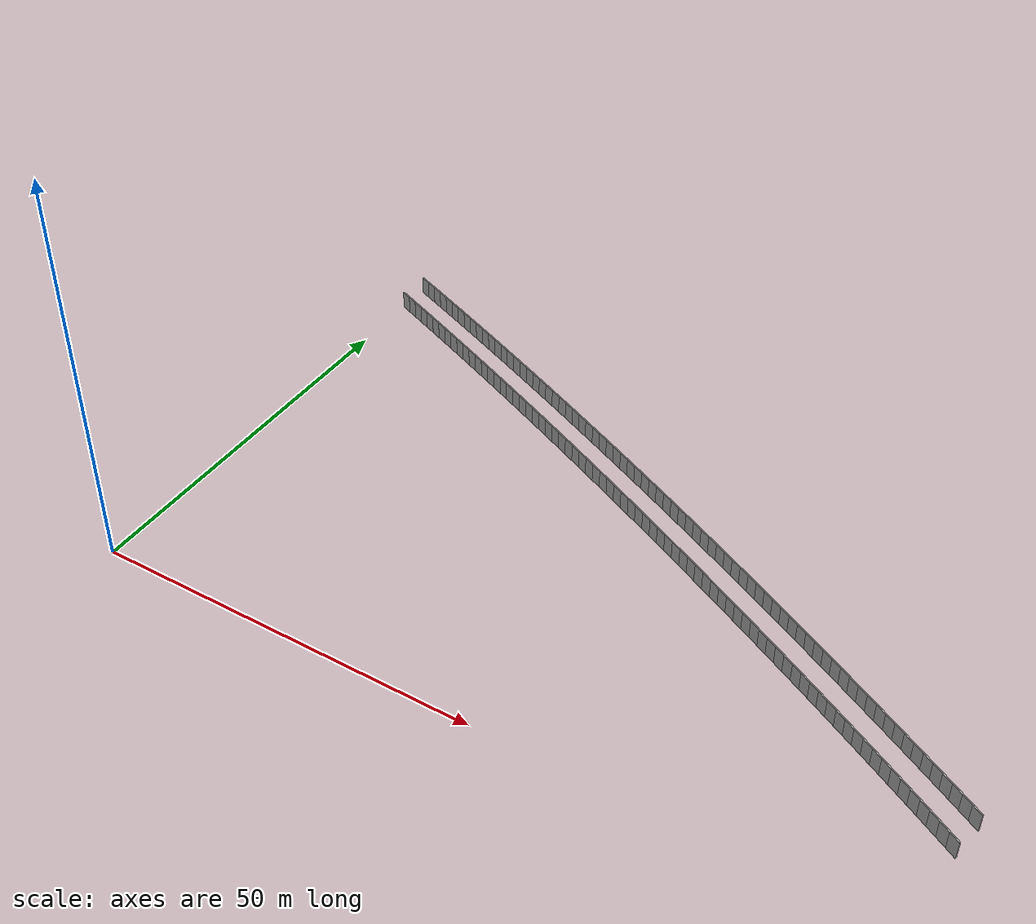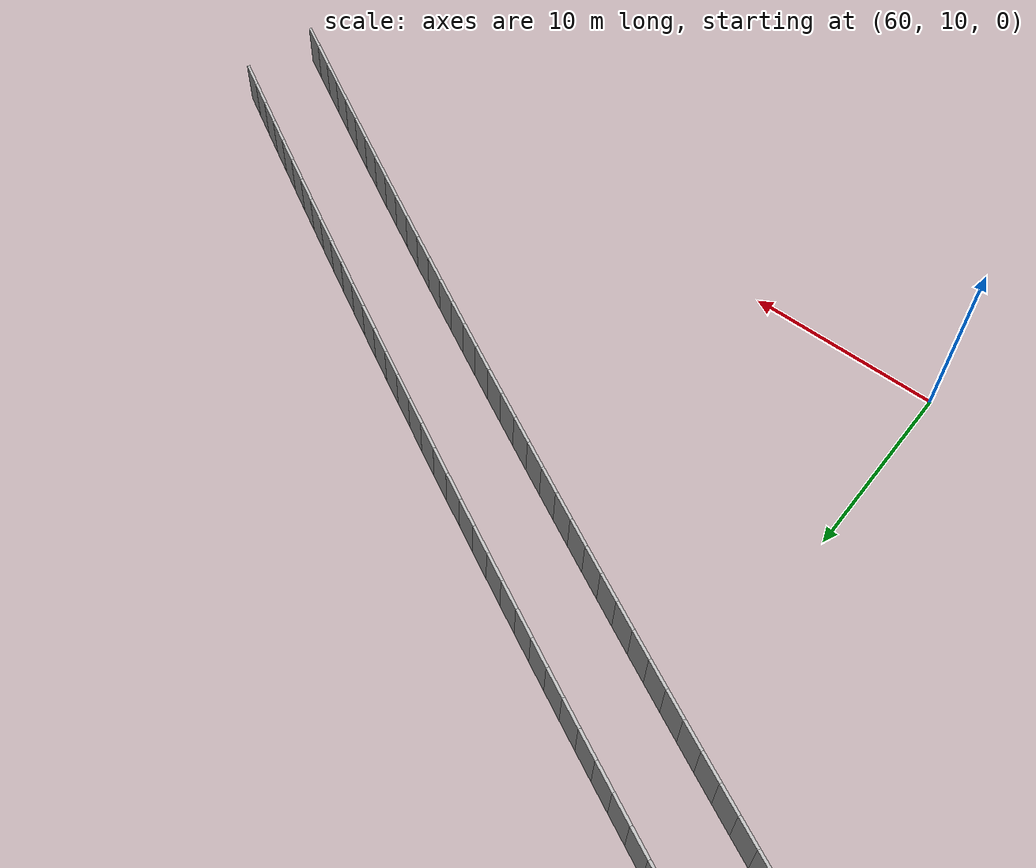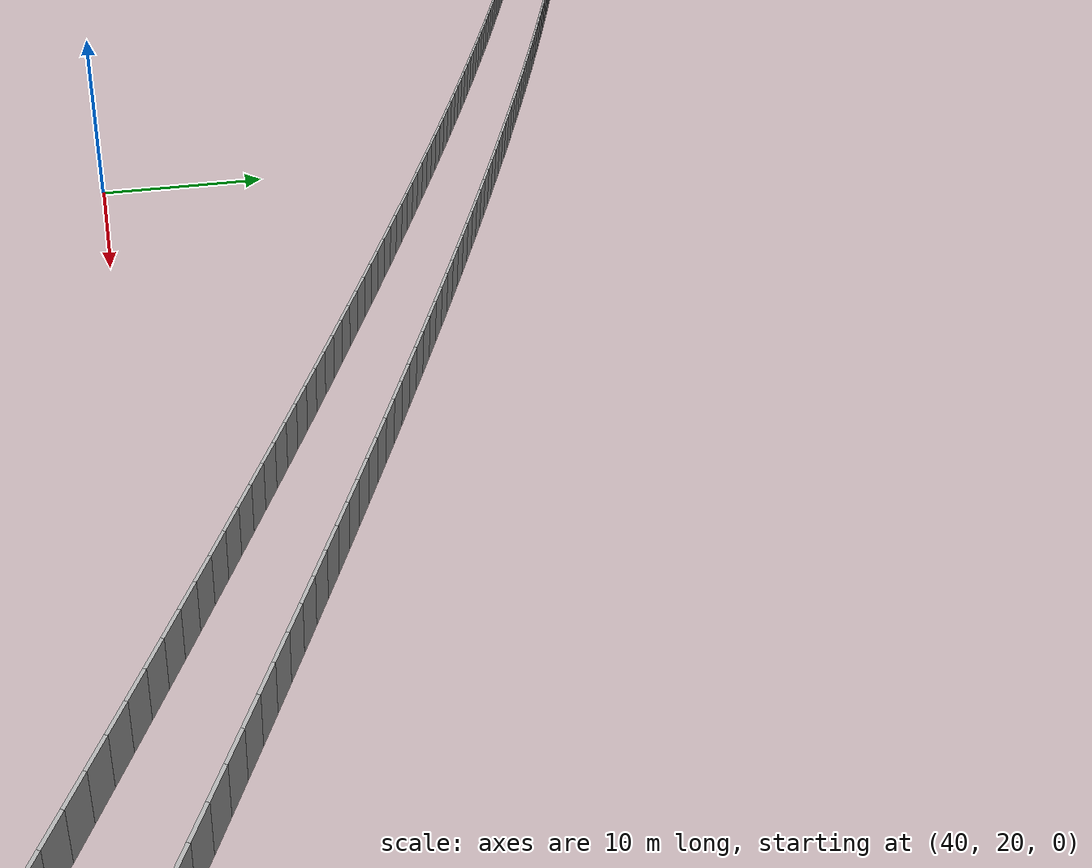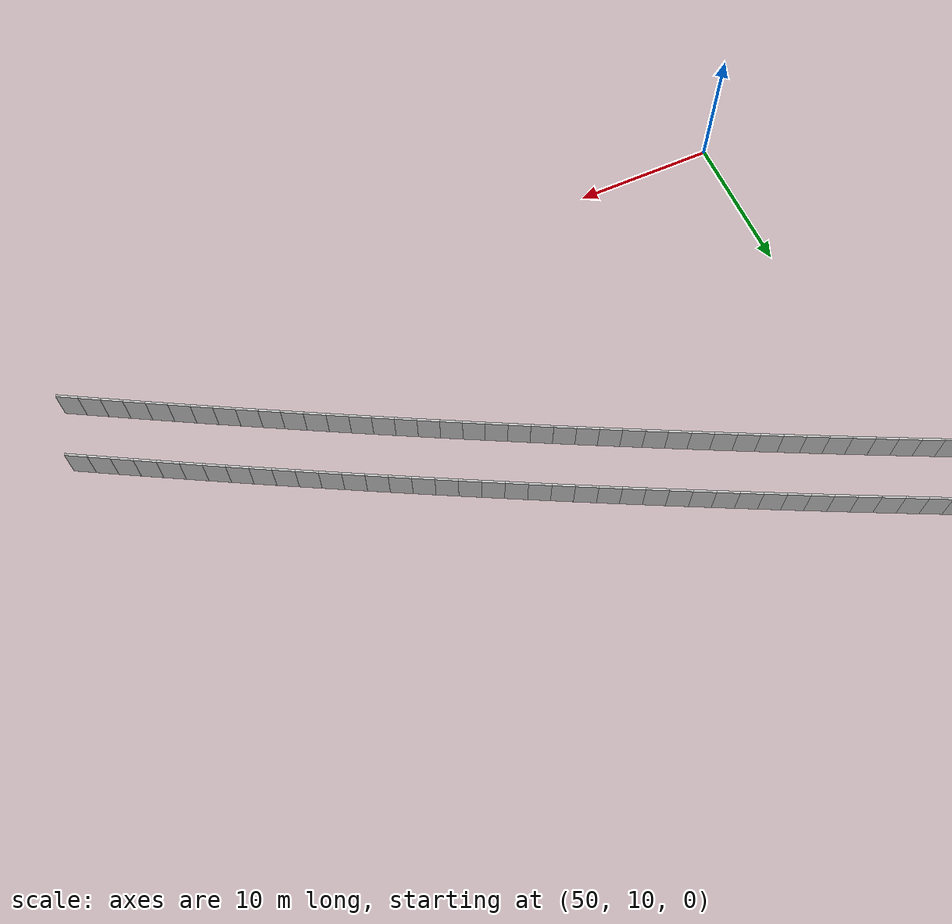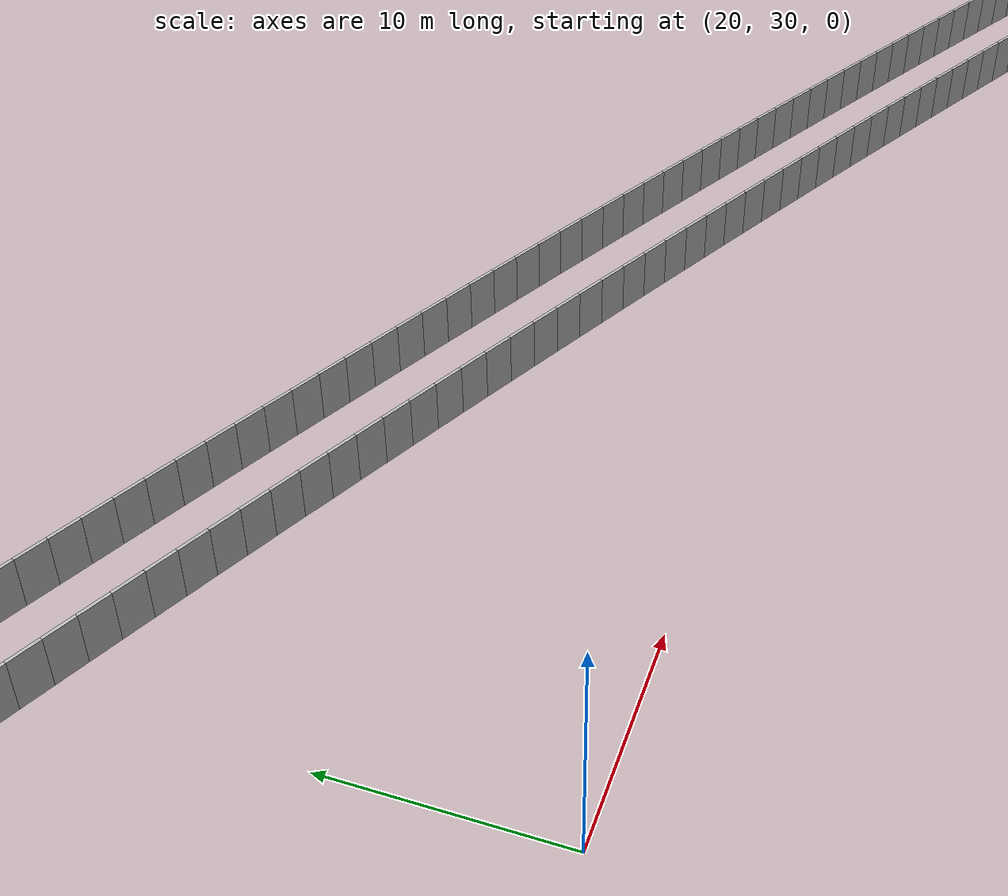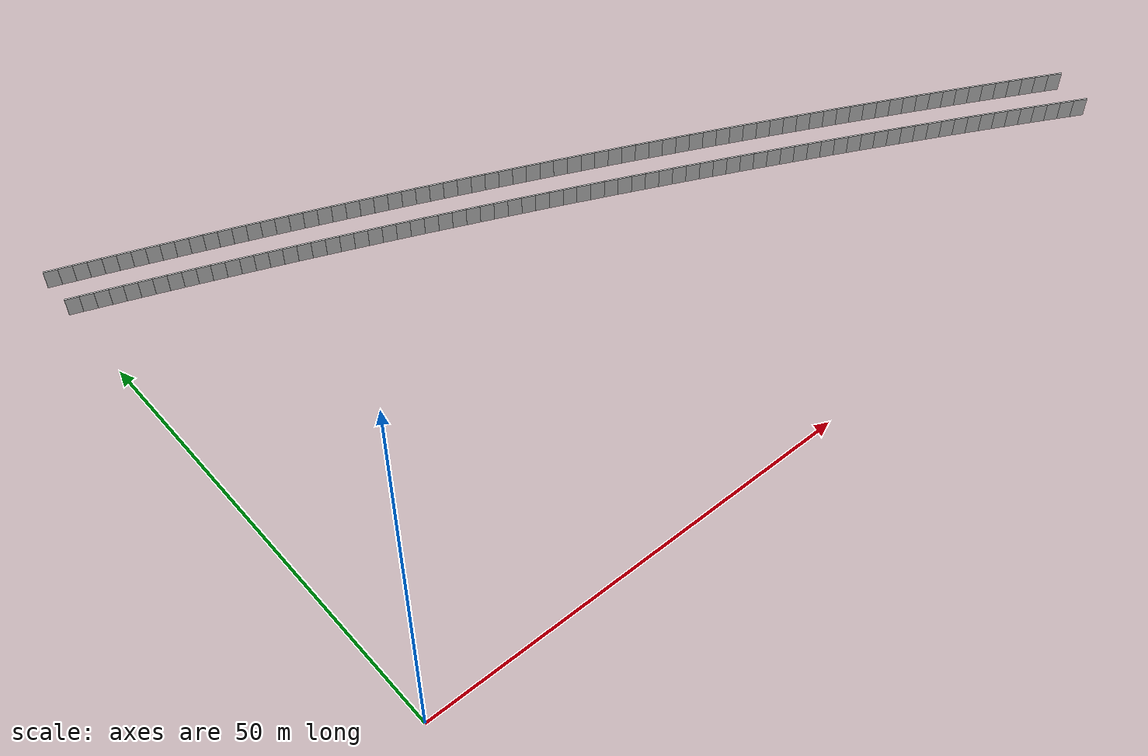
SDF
<?xml version="1.0" ?>
<sdf version="1.6">
  <model name="sps_1722">
    <pose frame="">0 0 0 0 -0 0</pose>
    <static>1</static>
    <self_collide>0</self_collide>
    <allow_auto_disable>0</allow_auto_disable>
    <link name="Wall10633">
      <kinematic>0</kinematic>
      <gravity>1</gravity>
      <self_collide>0</self_collide>
      <collision name="collision">
        <geometry>
          <box>
            <size>1.49658 0.15 2.5</size>
          </box>
        </geometry>
        <pose frame="">0 0 0 0 -0 0</pose>
      </collision>
      <visual name="visual">
        <geometry>
          <box>
            <size>1.49658 0.15 2.5</size>
          </box>
        </geometry>
        <pose frame="">0 0 0 0 -0 0</pose>
        <cast_shadows>1</cast_shadows>
        <transparency>0.0</transparency>
      </visual>
      <pose frame="">98.8934 11.6725 1.25 0 -0 2.63388</pose>
    </link>
    <link name="Wall10634">
      <kinematic>0</kinematic>
      <gravity>1</gravity>
      <self_collide>0</self_collide>
      <collision name="collision">
        <geometry>
          <box>
            <size>1.49649 0.15 2.5</size>
          </box>
        </geometry>
        <pose frame="">0 0 0 0 -0 0</pose>
      </collision>
      <visual name="visual">
        <geometry>
          <box>
            <size>1.49649 0.15 2.5</size>
          </box>
        </geometry>
        <pose frame="">0 0 0 0 -0 0</pose>
        <cast_shadows>1</cast_shadows>
        <transparency>0.0</transparency>
      </visual>
      <pose frame="">97.585 12.3989 1.25 0 -0 2.63567</pose>
    </link>
    <link name="Wall10635">
      <kinematic>0</kinematic>
      <gravity>1</gravity>
      <self_collide>0</self_collide>
      <collision name="collision">
        <geometry>
          <box>
            <size>1.49646 0.15 2.5</size>
          </box>
        </geometry>
        <pose frame="">0 0 0 0 -0 0</pose>
      </collision>
      <visual name="visual">
        <geometry>
          <box>
            <size>1.49646 0.15 2.5</size>
          </box>
        </geometry>
        <pose frame="">0 0 0 0 -0 0</pose>
        <cast_shadows>1</cast_shadows>
        <transparency>0.0</transparency>
      </visual>
      <pose frame="">96.2754 13.1232 1.25 0 -0 2.63706</pose>
    </link>
    <link name="Wall10636">
      <kinematic>0</kinematic>
      <gravity>1</gravity>
      <self_collide>0</self_collide>
      <collision name="collision">
        <geometry>
          <box>
            <size>1.49663 0.15 2.5</size>
          </box>
        </geometry>
        <pose frame="">0 0 0 0 -0 0</pose>
      </collision>
      <visual name="visual">
        <geometry>
          <box>
            <size>1.49663 0.15 2.5</size>
          </box>
        </geometry>
        <pose frame="">0 0 0 0 -0 0</pose>
        <cast_shadows>1</cast_shadows>
        <transparency>0.0</transparency>
      </visual>
      <pose frame="">94.9647 13.8455 1.25 0 -0 2.6388</pose>
    </link>
    <link name="Wall10637">
      <kinematic>0</kinematic>
      <gravity>1</gravity>
      <self_collide>0</self_collide>
      <collision name="collision">
        <geometry>
          <box>
            <size>1.49643 0.15 2.5</size>
          </box>
        </geometry>
        <pose frame="">0 0 0 0 -0 0</pose>
      </collision>
      <visual name="visual">
        <geometry>
          <box>
            <size>1.49643 0.15 2.5</size>
          </box>
        </geometry>
        <pose frame="">0 0 0 0 -0 0</pose>
        <cast_shadows>1</cast_shadows>
        <transparency>0.0</transparency>
      </visual>
      <pose frame="">93.6529 14.5656 1.25 0 -0 2.6404</pose>
    </link>
    <link name="Wall10638">
      <kinematic>0</kinematic>
      <gravity>1</gravity>
      <self_collide>0</self_collide>
      <collision name="collision">
        <geometry>
          <box>
            <size>1.49649 0.15 2.5</size>
          </box>
        </geometry>
        <pose frame="">0 0 0 0 -0 0</pose>
      </collision>
      <visual name="visual">
        <geometry>
          <box>
            <size>1.49649 0.15 2.5</size>
          </box>
        </geometry>
        <pose frame="">0 0 0 0 -0 0</pose>
        <cast_shadows>1</cast_shadows>
        <transparency>0.0</transparency>
      </visual>
      <pose frame="">92.34 15.2837 1.25 0 -0 2.64177</pose>
    </link>
    <link name="Wall10639">
      <kinematic>0</kinematic>
      <gravity>1</gravity>
      <self_collide>0</self_collide>
      <collision name="collision">
        <geometry>
          <box>
            <size>1.49655 0.15 2.5</size>
          </box>
        </geometry>
        <pose frame="">0 0 0 0 -0 0</pose>
      </collision>
      <visual name="visual">
        <geometry>
          <box>
            <size>1.49655 0.15 2.5</size>
          </box>
        </geometry>
        <pose frame="">0 0 0 0 -0 0</pose>
        <cast_shadows>1</cast_shadows>
        <transparency>0.0</transparency>
      </visual>
      <pose frame="">91.0258 15.9997 1.25 0 -0 2.64365</pose>
    </link>
    <link name="Wall10640">
      <kinematic>0</kinematic>
      <gravity>1</gravity>
      <self_collide>0</self_collide>
      <collision name="collision">
        <geometry>
          <box>
            <size>1.49656 0.15 2.5</size>
          </box>
        </geometry>
        <pose frame="">0 0 0 0 -0 0</pose>
      </collision>
      <visual name="visual">
        <geometry>
          <box>
            <size>1.49656 0.15 2.5</size>
          </box>
        </geometry>
        <pose frame="">0 0 0 0 -0 0</pose>
        <cast_shadows>1</cast_shadows>
        <transparency>0.0</transparency>
      </visual>
      <pose frame="">89.7105 16.7136 1.25 0 -0 2.645</pose>
    </link>
    <link name="Wall10641">
      <kinematic>0</kinematic>
      <gravity>1</gravity>
      <self_collide>0</self_collide>
      <collision name="collision">
        <geometry>
          <box>
            <size>1.49654 0.15 2.5</size>
          </box>
        </geometry>
        <pose frame="">0 0 0 0 -0 0</pose>
      </collision>
      <visual name="visual">
        <geometry>
          <box>
            <size>1.49654 0.15 2.5</size>
          </box>
        </geometry>
        <pose frame="">0 0 0 0 -0 0</pose>
        <cast_shadows>1</cast_shadows>
        <transparency>0.0</transparency>
      </visual>
      <pose frame="">88.3942 17.4255 1.25 0 -0 2.64666</pose>
    </link>
    <link name="Wall10642">
      <kinematic>0</kinematic>
      <gravity>1</gravity>
      <self_collide>0</self_collide>
      <collision name="collision">
        <geometry>
          <box>
            <size>1.49663 0.15 2.5</size>
          </box>
        </geometry>
        <pose frame="">0 0 0 0 -0 0</pose>
      </collision>
      <visual name="visual">
        <geometry>
          <box>
            <size>1.49663 0.15 2.5</size>
          </box>
        </geometry>
        <pose frame="">0 0 0 0 -0 0</pose>
        <cast_shadows>1</cast_shadows>
        <transparency>0.0</transparency>
      </visual>
      <pose frame="">87.0766 18.1352 1.25 0 -0 2.64836</pose>
    </link>
    <link name="Wall10643">
      <kinematic>0</kinematic>
      <gravity>1</gravity>
      <self_collide>0</self_collide>
      <collision name="collision">
        <geometry>
          <box>
            <size>1.49632 0.15 2.5</size>
          </box>
        </geometry>
        <pose frame="">0 0 0 0 -0 0</pose>
      </collision>
      <visual name="visual">
        <geometry>
          <box>
            <size>1.49632 0.15 2.5</size>
          </box>
        </geometry>
        <pose frame="">0 0 0 0 -0 0</pose>
        <cast_shadows>1</cast_shadows>
        <transparency>0.0</transparency>
      </visual>
      <pose frame="">85.758 18.8428 1.25 0 -0 2.64978</pose>
    </link>
    <link name="Wall10644">
      <kinematic>0</kinematic>
      <gravity>1</gravity>
      <self_collide>0</self_collide>
      <collision name="collision">
        <geometry>
          <box>
            <size>1.49655 0.15 2.5</size>
          </box>
        </geometry>
        <pose frame="">0 0 0 0 -0 0</pose>
      </collision>
      <visual name="visual">
        <geometry>
          <box>
            <size>1.49655 0.15 2.5</size>
          </box>
        </geometry>
        <pose frame="">0 0 0 0 -0 0</pose>
        <cast_shadows>1</cast_shadows>
        <transparency>0.0</transparency>
      </visual>
      <pose frame="">84.4383 19.5483 1.25 0 -0 2.65157</pose>
    </link>
    <link name="Wall10645">
      <kinematic>0</kinematic>
      <gravity>1</gravity>
      <self_collide>0</self_collide>
      <collision name="collision">
        <geometry>
          <box>
            <size>1.49652 0.15 2.5</size>
          </box>
        </geometry>
        <pose frame="">0 0 0 0 -0 0</pose>
      </collision>
      <visual name="visual">
        <geometry>
          <box>
            <size>1.49652 0.15 2.5</size>
          </box>
        </geometry>
        <pose frame="">0 0 0 0 -0 0</pose>
        <cast_shadows>1</cast_shadows>
        <transparency>0.0</transparency>
      </visual>
      <pose frame="">83.1173 20.2517 1.25 0 -0 2.65299</pose>
    </link>
    <link name="Wall10646">
      <kinematic>0</kinematic>
      <gravity>1</gravity>
      <self_collide>0</self_collide>
      <collision name="collision">
        <geometry>
          <box>
            <size>1.49641 0.15 2.5</size>
          </box>
        </geometry>
        <pose frame="">0 0 0 0 -0 0</pose>
      </collision>
      <visual name="visual">
        <geometry>
          <box>
            <size>1.49641 0.15 2.5</size>
          </box>
        </geometry>
        <pose frame="">0 0 0 0 -0 0</pose>
        <cast_shadows>1</cast_shadows>
        <transparency>0.0</transparency>
      </visual>
      <pose frame="">81.7954 20.9531 1.25 0 -0 2.65452</pose>
    </link>
    <link name="Wall10647">
      <kinematic>0</kinematic>
      <gravity>1</gravity>
      <self_collide>0</self_collide>
      <collision name="collision">
        <geometry>
          <box>
            <size>1.49662 0.15 2.5</size>
          </box>
        </geometry>
        <pose frame="">0 0 0 0 -0 0</pose>
      </collision>
      <visual name="visual">
        <geometry>
          <box>
            <size>1.49662 0.15 2.5</size>
          </box>
        </geometry>
        <pose frame="">0 0 0 0 -0 0</pose>
        <cast_shadows>1</cast_shadows>
        <transparency>0.0</transparency>
      </visual>
      <pose frame="">80.4723 21.6524 1.25 0 -0 2.65626</pose>
    </link>
    <link name="Wall10648">
      <kinematic>0</kinematic>
      <gravity>1</gravity>
      <self_collide>0</self_collide>
      <collision name="collision">
        <geometry>
          <box>
            <size>1.49646 0.15 2.5</size>
          </box>
        </geometry>
        <pose frame="">0 0 0 0 -0 0</pose>
      </collision>
      <visual name="visual">
        <geometry>
          <box>
            <size>1.49646 0.15 2.5</size>
          </box>
        </geometry>
        <pose frame="">0 0 0 0 -0 0</pose>
        <cast_shadows>1</cast_shadows>
        <transparency>0.0</transparency>
      </visual>
      <pose frame="">79.1481 22.3495 1.25 0 -0 2.65786</pose>
    </link>
    <link name="Wall10649">
      <kinematic>0</kinematic>
      <gravity>1</gravity>
      <self_collide>0</self_collide>
      <collision name="collision">
        <geometry>
          <box>
            <size>1.49656 0.15 2.5</size>
          </box>
        </geometry>
        <pose frame="">0 0 0 0 -0 0</pose>
      </collision>
      <visual name="visual">
        <geometry>
          <box>
            <size>1.49656 0.15 2.5</size>
          </box>
        </geometry>
        <pose frame="">0 0 0 0 -0 0</pose>
        <cast_shadows>1</cast_shadows>
        <transparency>0.0</transparency>
      </visual>
      <pose frame="">77.8228 23.0446 1.25 0 -0 2.65923</pose>
    </link>
    <link name="Wall10650">
      <kinematic>0</kinematic>
      <gravity>1</gravity>
      <self_collide>0</self_collide>
      <collision name="collision">
        <geometry>
          <box>
            <size>1.49654 0.15 2.5</size>
          </box>
        </geometry>
        <pose frame="">0 0 0 0 -0 0</pose>
      </collision>
      <visual name="visual">
        <geometry>
          <box>
            <size>1.49654 0.15 2.5</size>
          </box>
        </geometry>
        <pose frame="">0 0 0 0 -0 0</pose>
        <cast_shadows>1</cast_shadows>
        <transparency>0.0</transparency>
      </visual>
      <pose frame="">76.4964 23.7376 1.25 0 -0 2.66102</pose>
    </link>
    <link name="Wall10651">
      <kinematic>0</kinematic>
      <gravity>1</gravity>
      <self_collide>0</self_collide>
      <collision name="collision">
        <geometry>
          <box>
            <size>1.49645 0.15 2.5</size>
          </box>
        </geometry>
        <pose frame="">0 0 0 0 -0 0</pose>
      </collision>
      <visual name="visual">
        <geometry>
          <box>
            <size>1.49645 0.15 2.5</size>
          </box>
        </geometry>
        <pose frame="">0 0 0 0 -0 0</pose>
        <cast_shadows>1</cast_shadows>
        <transparency>0.0</transparency>
      </visual>
      <pose frame="">75.1688 24.4284 1.25 0 -0 2.66255</pose>
    </link>
    <link name="Wall10652">
      <kinematic>0</kinematic>
      <gravity>1</gravity>
      <self_collide>0</self_collide>
      <collision name="collision">
        <geometry>
          <box>
            <size>1.49658 0.15 2.5</size>
          </box>
        </geometry>
        <pose frame="">0 0 0 0 -0 0</pose>
      </collision>
      <visual name="visual">
        <geometry>
          <box>
            <size>1.49658 0.15 2.5</size>
          </box>
        </geometry>
        <pose frame="">0 0 0 0 -0 0</pose>
        <cast_shadows>1</cast_shadows>
        <transparency>0.0</transparency>
      </visual>
      <pose frame="">73.8403 25.1172 1.25 0 -0 2.66406</pose>
    </link>
    <link name="Wall10653">
      <kinematic>0</kinematic>
      <gravity>1</gravity>
      <self_collide>0</self_collide>
      <collision name="collision">
        <geometry>
          <box>
            <size>1.49633 0.15 2.5</size>
          </box>
        </geometry>
        <pose frame="">0 0 0 0 -0 0</pose>
      </collision>
      <visual name="visual">
        <geometry>
          <box>
            <size>1.49633 0.15 2.5</size>
          </box>
        </geometry>
        <pose frame="">0 0 0 0 -0 0</pose>
        <cast_shadows>1</cast_shadows>
        <transparency>0.0</transparency>
      </visual>
      <pose frame="">72.5107 25.8039 1.25 0 -0 2.66563</pose>
    </link>
    <link name="Wall10654">
      <kinematic>0</kinematic>
      <gravity>1</gravity>
      <self_collide>0</self_collide>
      <collision name="collision">
        <geometry>
          <box>
            <size>1.49666 0.15 2.5</size>
          </box>
        </geometry>
        <pose frame="">0 0 0 0 -0 0</pose>
      </collision>
      <visual name="visual">
        <geometry>
          <box>
            <size>1.49666 0.15 2.5</size>
          </box>
        </geometry>
        <pose frame="">0 0 0 0 -0 0</pose>
        <cast_shadows>1</cast_shadows>
        <transparency>0.0</transparency>
      </visual>
      <pose frame="">71.18 26.4885 1.25 0 -0 2.66726</pose>
    </link>
    <link name="Wall10655">
      <kinematic>0</kinematic>
      <gravity>1</gravity>
      <self_collide>0</self_collide>
      <collision name="collision">
        <geometry>
          <box>
            <size>1.49652 0.15 2.5</size>
          </box>
        </geometry>
        <pose frame="">0 0 0 0 -0 0</pose>
      </collision>
      <visual name="visual">
        <geometry>
          <box>
            <size>1.49652 0.15 2.5</size>
          </box>
        </geometry>
        <pose frame="">0 0 0 0 -0 0</pose>
        <cast_shadows>1</cast_shadows>
        <transparency>0.0</transparency>
      </visual>
      <pose frame="">69.848 27.171 1.25 0 -0 2.66886</pose>
    </link>
    <link name="Wall10656">
      <kinematic>0</kinematic>
      <gravity>1</gravity>
      <self_collide>0</self_collide>
      <collision name="collision">
        <geometry>
          <box>
            <size>1.49639 0.15 2.5</size>
          </box>
        </geometry>
        <pose frame="">0 0 0 0 -0 0</pose>
      </collision>
      <visual name="visual">
        <geometry>
          <box>
            <size>1.49639 0.15 2.5</size>
          </box>
        </geometry>
        <pose frame="">0 0 0 0 -0 0</pose>
        <cast_shadows>1</cast_shadows>
        <transparency>0.0</transparency>
      </visual>
      <pose frame="">68.5152 27.8513 1.25 0 -0 2.67047</pose>
    </link>
    <link name="Wall10657">
      <kinematic>0</kinematic>
      <gravity>1</gravity>
      <self_collide>0</self_collide>
      <collision name="collision">
        <geometry>
          <box>
            <size>1.4966 0.15 2.5</size>
          </box>
        </geometry>
        <pose frame="">0 0 0 0 -0 0</pose>
      </collision>
      <visual name="visual">
        <geometry>
          <box>
            <size>1.4966 0.15 2.5</size>
          </box>
        </geometry>
        <pose frame="">0 0 0 0 -0 0</pose>
        <cast_shadows>1</cast_shadows>
        <transparency>0.0</transparency>
      </visual>
      <pose frame="">67.1812 28.5295 1.25 0 -0 2.672</pose>
    </link>
    <link name="Wall10658">
      <kinematic>0</kinematic>
      <gravity>1</gravity>
      <self_collide>0</self_collide>
      <collision name="collision">
        <geometry>
          <box>
            <size>1.49659 0.15 2.5</size>
          </box>
        </geometry>
        <pose frame="">0 0 0 0 -0 0</pose>
      </collision>
      <visual name="visual">
        <geometry>
          <box>
            <size>1.49659 0.15 2.5</size>
          </box>
        </geometry>
        <pose frame="">0 0 0 0 -0 0</pose>
        <cast_shadows>1</cast_shadows>
        <transparency>0.0</transparency>
      </visual>
      <pose frame="">65.8461 29.2057 1.25 0 -0 2.67355</pose>
    </link>
    <link name="Wall10659">
      <kinematic>0</kinematic>
      <gravity>1</gravity>
      <self_collide>0</self_collide>
      <collision name="collision">
        <geometry>
          <box>
            <size>1.49639 0.15 2.5</size>
          </box>
        </geometry>
        <pose frame="">0 0 0 0 -0 0</pose>
      </collision>
      <visual name="visual">
        <geometry>
          <box>
            <size>1.49639 0.15 2.5</size>
          </box>
        </geometry>
        <pose frame="">0 0 0 0 -0 0</pose>
        <cast_shadows>1</cast_shadows>
        <transparency>0.0</transparency>
      </visual>
      <pose frame="">64.5099 29.8797 1.25 0 -0 2.67526</pose>
    </link>
    <link name="Wall10660">
      <kinematic>0</kinematic>
      <gravity>1</gravity>
      <self_collide>0</self_collide>
      <collision name="collision">
        <geometry>
          <box>
            <size>1.49655 0.15 2.5</size>
          </box>
        </geometry>
        <pose frame="">0 0 0 0 -0 0</pose>
      </collision>
      <visual name="visual">
        <geometry>
          <box>
            <size>1.49655 0.15 2.5</size>
          </box>
        </geometry>
        <pose frame="">0 0 0 0 -0 0</pose>
        <cast_shadows>1</cast_shadows>
        <transparency>0.0</transparency>
      </visual>
      <pose frame="">63.1728 30.5515 1.25 0 -0 2.67678</pose>
    </link>
    <link name="Wall10661">
      <kinematic>0</kinematic>
      <gravity>1</gravity>
      <self_collide>0</self_collide>
      <collision name="collision">
        <geometry>
          <box>
            <size>1.49654 0.15 2.5</size>
          </box>
        </geometry>
        <pose frame="">0 0 0 0 -0 0</pose>
      </collision>
      <visual name="visual">
        <geometry>
          <box>
            <size>1.49654 0.15 2.5</size>
          </box>
        </geometry>
        <pose frame="">0 0 0 0 -0 0</pose>
        <cast_shadows>1</cast_shadows>
        <transparency>0.0</transparency>
      </visual>
      <pose frame="">61.8345 31.2213 1.25 0 -0 2.67833</pose>
    </link>
    <link name="Wall10662">
      <kinematic>0</kinematic>
      <gravity>1</gravity>
      <self_collide>0</self_collide>
      <collision name="collision">
        <geometry>
          <box>
            <size>1.49668 0.15 2.5</size>
          </box>
        </geometry>
        <pose frame="">0 0 0 0 -0 0</pose>
      </collision>
      <visual name="visual">
        <geometry>
          <box>
            <size>1.49668 0.15 2.5</size>
          </box>
        </geometry>
        <pose frame="">0 0 0 0 -0 0</pose>
        <cast_shadows>1</cast_shadows>
        <transparency>0.0</transparency>
      </visual>
      <pose frame="">60.495 31.889 1.25 0 -0 2.67997</pose>
    </link>
    <link name="Wall10663">
      <kinematic>0</kinematic>
      <gravity>1</gravity>
      <self_collide>0</self_collide>
      <collision name="collision">
        <geometry>
          <box>
            <size>1.49634 0.15 2.5</size>
          </box>
        </geometry>
        <pose frame="">0 0 0 0 -0 0</pose>
      </collision>
      <visual name="visual">
        <geometry>
          <box>
            <size>1.49634 0.15 2.5</size>
          </box>
        </geometry>
        <pose frame="">0 0 0 0 -0 0</pose>
        <cast_shadows>1</cast_shadows>
        <transparency>0.0</transparency>
      </visual>
      <pose frame="">59.1547 32.5545 1.25 0 -0 2.68154</pose>
    </link>
    <link name="Wall10664">
      <kinematic>0</kinematic>
      <gravity>1</gravity>
      <self_collide>0</self_collide>
      <collision name="collision">
        <geometry>
          <box>
            <size>1.49654 0.15 2.5</size>
          </box>
        </geometry>
        <pose frame="">0 0 0 0 -0 0</pose>
      </collision>
      <visual name="visual">
        <geometry>
          <box>
            <size>1.49654 0.15 2.5</size>
          </box>
        </geometry>
        <pose frame="">0 0 0 0 -0 0</pose>
        <cast_shadows>1</cast_shadows>
        <transparency>0.0</transparency>
      </visual>
      <pose frame="">57.8133 33.2178 1.25 0 -0 2.6832</pose>
    </link>
    <link name="Wall10665">
      <kinematic>0</kinematic>
      <gravity>1</gravity>
      <self_collide>0</self_collide>
      <collision name="collision">
        <geometry>
          <box>
            <size>1.49647 0.15 2.5</size>
          </box>
        </geometry>
        <pose frame="">0 0 0 0 -0 0</pose>
      </collision>
      <visual name="visual">
        <geometry>
          <box>
            <size>1.49647 0.15 2.5</size>
          </box>
        </geometry>
        <pose frame="">0 0 0 0 -0 0</pose>
        <cast_shadows>1</cast_shadows>
        <transparency>0.0</transparency>
      </visual>
      <pose frame="">56.4708 33.879 1.25 0 -0 2.68468</pose>
    </link>
    <link name="Wall10666">
      <kinematic>0</kinematic>
      <gravity>1</gravity>
      <self_collide>0</self_collide>
      <collision name="collision">
        <geometry>
          <box>
            <size>1.49641 0.15 2.5</size>
          </box>
        </geometry>
        <pose frame="">0 0 0 0 -0 0</pose>
      </collision>
      <visual name="visual">
        <geometry>
          <box>
            <size>1.49641 0.15 2.5</size>
          </box>
        </geometry>
        <pose frame="">0 0 0 0 -0 0</pose>
        <cast_shadows>1</cast_shadows>
        <transparency>0.0</transparency>
      </visual>
      <pose frame="">55.1273 34.5381 1.25 0 -0 2.68634</pose>
    </link>
    <link name="Wall10667">
      <kinematic>0</kinematic>
      <gravity>1</gravity>
      <self_collide>0</self_collide>
      <collision name="collision">
        <geometry>
          <box>
            <size>1.49673 0.15 2.5</size>
          </box>
        </geometry>
        <pose frame="">0 0 0 0 -0 0</pose>
      </collision>
      <visual name="visual">
        <geometry>
          <box>
            <size>1.49673 0.15 2.5</size>
          </box>
        </geometry>
        <pose frame="">0 0 0 0 -0 0</pose>
        <cast_shadows>1</cast_shadows>
        <transparency>0.0</transparency>
      </visual>
      <pose frame="">53.7827 35.1952 1.25 0 -0 2.68776</pose>
    </link>
    <link name="Wall10668">
      <kinematic>0</kinematic>
      <gravity>1</gravity>
      <self_collide>0</self_collide>
      <collision name="collision">
        <geometry>
          <box>
            <size>1.4964 0.15 2.5</size>
          </box>
        </geometry>
        <pose frame="">0 0 0 0 -0 0</pose>
      </collision>
      <visual name="visual">
        <geometry>
          <box>
            <size>1.4964 0.15 2.5</size>
          </box>
        </geometry>
        <pose frame="">0 0 0 0 -0 0</pose>
        <cast_shadows>1</cast_shadows>
        <transparency>0.0</transparency>
      </visual>
      <pose frame="">52.4371 35.8502 1.25 0 -0 2.68942</pose>
    </link>
    <link name="Wall10669">
      <kinematic>0</kinematic>
      <gravity>1</gravity>
      <self_collide>0</self_collide>
      <collision name="collision">
        <geometry>
          <box>
            <size>1.49654 0.15 2.5</size>
          </box>
        </geometry>
        <pose frame="">0 0 0 0 -0 0</pose>
      </collision>
      <visual name="visual">
        <geometry>
          <box>
            <size>1.49654 0.15 2.5</size>
          </box>
        </geometry>
        <pose frame="">0 0 0 0 -0 0</pose>
        <cast_shadows>1</cast_shadows>
        <transparency>0.0</transparency>
      </visual>
      <pose frame="">51.0904 36.5029 1.25 0 -0 2.6911</pose>
    </link>
    <link name="Wall10670">
      <kinematic>0</kinematic>
      <gravity>1</gravity>
      <self_collide>0</self_collide>
      <collision name="collision">
        <geometry>
          <box>
            <size>1.49646 0.15 2.5</size>
          </box>
        </geometry>
        <pose frame="">0 0 0 0 -0 0</pose>
      </collision>
      <visual name="visual">
        <geometry>
          <box>
            <size>1.49646 0.15 2.5</size>
          </box>
        </geometry>
        <pose frame="">0 0 0 0 -0 0</pose>
        <cast_shadows>1</cast_shadows>
        <transparency>0.0</transparency>
      </visual>
      <pose frame="">49.7427 37.1534 1.25 0 -0 2.6927</pose>
    </link>
    <link name="Wall10671">
      <kinematic>0</kinematic>
      <gravity>1</gravity>
      <self_collide>0</self_collide>
      <collision name="collision">
        <geometry>
          <box>
            <size>1.49647 0.15 2.5</size>
          </box>
        </geometry>
        <pose frame="">0 0 0 0 -0 0</pose>
      </collision>
      <visual name="visual">
        <geometry>
          <box>
            <size>1.49647 0.15 2.5</size>
          </box>
        </geometry>
        <pose frame="">0 0 0 0 -0 0</pose>
        <cast_shadows>1</cast_shadows>
        <transparency>0.0</transparency>
      </visual>
      <pose frame="">48.394 37.8018 1.25 0 -0 2.6942</pose>
    </link>
    <link name="Wall10672">
      <kinematic>0</kinematic>
      <gravity>1</gravity>
      <self_collide>0</self_collide>
      <collision name="collision">
        <geometry>
          <box>
            <size>1.4967 0.15 2.5</size>
          </box>
        </geometry>
        <pose frame="">0 0 0 0 -0 0</pose>
      </collision>
      <visual name="visual">
        <geometry>
          <box>
            <size>1.4967 0.15 2.5</size>
          </box>
        </geometry>
        <pose frame="">0 0 0 0 -0 0</pose>
        <cast_shadows>1</cast_shadows>
        <transparency>0.0</transparency>
      </visual>
      <pose frame="">47.0442 38.4482 1.25 0 -0 2.69576</pose>
    </link>
    <link name="Wall10673">
      <kinematic>0</kinematic>
      <gravity>1</gravity>
      <self_collide>0</self_collide>
      <collision name="collision">
        <geometry>
          <box>
            <size>1.49639 0.15 2.5</size>
          </box>
        </geometry>
        <pose frame="">0 0 0 0 -0 0</pose>
      </collision>
      <visual name="visual">
        <geometry>
          <box>
            <size>1.49639 0.15 2.5</size>
          </box>
        </geometry>
        <pose frame="">0 0 0 0 -0 0</pose>
        <cast_shadows>1</cast_shadows>
        <transparency>0.0</transparency>
      </visual>
      <pose frame="">45.6934 39.0924 1.25 0 -0 2.69743</pose>
    </link>
    <link name="Wall10674">
      <kinematic>0</kinematic>
      <gravity>1</gravity>
      <self_collide>0</self_collide>
      <collision name="collision">
        <geometry>
          <box>
            <size>1.49663 0.15 2.5</size>
          </box>
        </geometry>
        <pose frame="">0 0 0 0 -0 0</pose>
      </collision>
      <visual name="visual">
        <geometry>
          <box>
            <size>1.49663 0.15 2.5</size>
          </box>
        </geometry>
        <pose frame="">0 0 0 0 -0 0</pose>
        <cast_shadows>1</cast_shadows>
        <transparency>0.0</transparency>
      </visual>
      <pose frame="">44.3416 39.7344 1.25 0 -0 2.69899</pose>
    </link>
    <link name="Wall10675">
      <kinematic>0</kinematic>
      <gravity>1</gravity>
      <self_collide>0</self_collide>
      <collision name="collision">
        <geometry>
          <box>
            <size>1.49635 0.15 2.5</size>
          </box>
        </geometry>
        <pose frame="">0 0 0 0 -0 0</pose>
      </collision>
      <visual name="visual">
        <geometry>
          <box>
            <size>1.49635 0.15 2.5</size>
          </box>
        </geometry>
        <pose frame="">0 0 0 0 -0 0</pose>
        <cast_shadows>1</cast_shadows>
        <transparency>0.0</transparency>
      </visual>
      <pose frame="">42.9889 40.3743 1.25 0 -0 2.70053</pose>
    </link>
    <link name="Wall10676">
      <kinematic>0</kinematic>
      <gravity>1</gravity>
      <self_collide>0</self_collide>
      <collision name="collision">
        <geometry>
          <box>
            <size>1.49651 0.15 2.5</size>
          </box>
        </geometry>
        <pose frame="">0 0 0 0 -0 0</pose>
      </collision>
      <visual name="visual">
        <geometry>
          <box>
            <size>1.49651 0.15 2.5</size>
          </box>
        </geometry>
        <pose frame="">0 0 0 0 -0 0</pose>
        <cast_shadows>1</cast_shadows>
        <transparency>0.0</transparency>
      </visual>
      <pose frame="">41.6352 41.0121 1.25 0 -0 2.70202</pose>
    </link>
    <link name="Wall10677">
      <kinematic>0</kinematic>
      <gravity>1</gravity>
      <self_collide>0</self_collide>
      <collision name="collision">
        <geometry>
          <box>
            <size>1.49647 0.15 2.5</size>
          </box>
        </geometry>
        <pose frame="">0 0 0 0 -0 0</pose>
      </collision>
      <visual name="visual">
        <geometry>
          <box>
            <size>1.49647 0.15 2.5</size>
          </box>
        </geometry>
        <pose frame="">0 0 0 0 -0 0</pose>
        <cast_shadows>1</cast_shadows>
        <transparency>0.0</transparency>
      </visual>
      <pose frame="">40.2804 41.6477 1.25 0 -0 2.70381</pose>
    </link>
    <link name="Wall10678">
      <kinematic>0</kinematic>
      <gravity>1</gravity>
      <self_collide>0</self_collide>
      <collision name="collision">
        <geometry>
          <box>
            <size>1.49669 0.15 2.5</size>
          </box>
        </geometry>
        <pose frame="">0 0 0 0 -0 0</pose>
      </collision>
      <visual name="visual">
        <geometry>
          <box>
            <size>1.49669 0.15 2.5</size>
          </box>
        </geometry>
        <pose frame="">0 0 0 0 -0 0</pose>
        <cast_shadows>1</cast_shadows>
        <transparency>0.0</transparency>
      </visual>
      <pose frame="">38.9245 42.2812 1.25 0 -0 2.70523</pose>
    </link>
    <link name="Wall10679">
      <kinematic>0</kinematic>
      <gravity>1</gravity>
      <self_collide>0</self_collide>
      <collision name="collision">
        <geometry>
          <box>
            <size>1.49635 0.15 2.5</size>
          </box>
        </geometry>
        <pose frame="">0 0 0 0 -0 0</pose>
      </collision>
      <visual name="visual">
        <geometry>
          <box>
            <size>1.49635 0.15 2.5</size>
          </box>
        </geometry>
        <pose frame="">0 0 0 0 -0 0</pose>
        <cast_shadows>1</cast_shadows>
        <transparency>0.0</transparency>
      </visual>
      <pose frame="">37.5676 42.9126 1.25 0 -0 2.70688</pose>
    </link>
    <link name="Wall10680">
      <kinematic>0</kinematic>
      <gravity>1</gravity>
      <self_collide>0</self_collide>
      <collision name="collision">
        <geometry>
          <box>
            <size>1.49664 0.15 2.5</size>
          </box>
        </geometry>
        <pose frame="">0 0 0 0 -0 0</pose>
      </collision>
      <visual name="visual">
        <geometry>
          <box>
            <size>1.49664 0.15 2.5</size>
          </box>
        </geometry>
        <pose frame="">0 0 0 0 -0 0</pose>
        <cast_shadows>1</cast_shadows>
        <transparency>0.0</transparency>
      </visual>
      <pose frame="">36.2099 43.5418 1.25 0 -0 2.70841</pose>
    </link>
    <link name="Wall10681">
      <kinematic>0</kinematic>
      <gravity>1</gravity>
      <self_collide>0</self_collide>
      <collision name="collision">
        <geometry>
          <box>
            <size>1.49663 0.15 2.5</size>
          </box>
        </geometry>
        <pose frame="">0 0 0 0 -0 0</pose>
      </collision>
      <visual name="visual">
        <geometry>
          <box>
            <size>1.49663 0.15 2.5</size>
          </box>
        </geometry>
        <pose frame="">0 0 0 0 -0 0</pose>
        <cast_shadows>1</cast_shadows>
        <transparency>0.0</transparency>
      </visual>
      <pose frame="">34.8509 44.1689 1.25 0 -0 2.71007</pose>
    </link>
    <link name="Wall10682">
      <kinematic>0</kinematic>
      <gravity>1</gravity>
      <self_collide>0</self_collide>
      <collision name="collision">
        <geometry>
          <box>
            <size>1.49638 0.15 2.5</size>
          </box>
        </geometry>
        <pose frame="">0 0 0 0 -0 0</pose>
      </collision>
      <visual name="visual">
        <geometry>
          <box>
            <size>1.49638 0.15 2.5</size>
          </box>
        </geometry>
        <pose frame="">0 0 0 0 -0 0</pose>
        <cast_shadows>1</cast_shadows>
        <transparency>0.0</transparency>
      </visual>
      <pose frame="">33.4911 44.7938 1.25 0 -0 2.71161</pose>
    </link>
    <link name="Wall10683">
      <kinematic>0</kinematic>
      <gravity>1</gravity>
      <self_collide>0</self_collide>
      <collision name="collision">
        <geometry>
          <box>
            <size>1.4966 0.15 2.5</size>
          </box>
        </geometry>
        <pose frame="">0 0 0 0 -0 0</pose>
      </collision>
      <visual name="visual">
        <geometry>
          <box>
            <size>1.4966 0.15 2.5</size>
          </box>
        </geometry>
        <pose frame="">0 0 0 0 -0 0</pose>
        <cast_shadows>1</cast_shadows>
        <transparency>0.0</transparency>
      </visual>
      <pose frame="">32.1304 45.4165 1.25 0 -0 2.71324</pose>
    </link>
    <link name="Wall10684">
      <kinematic>0</kinematic>
      <gravity>1</gravity>
      <self_collide>0</self_collide>
      <collision name="collision">
        <geometry>
          <box>
            <size>1.49639 0.15 2.5</size>
          </box>
        </geometry>
        <pose frame="">0 0 0 0 -0 0</pose>
      </collision>
      <visual name="visual">
        <geometry>
          <box>
            <size>1.49639 0.15 2.5</size>
          </box>
        </geometry>
        <pose frame="">0 0 0 0 -0 0</pose>
        <cast_shadows>1</cast_shadows>
        <transparency>0.0</transparency>
      </visual>
      <pose frame="">30.7686 46.037 1.25 0 -0 2.71484</pose>
    </link>
    <link name="Wall10685">
      <kinematic>0</kinematic>
      <gravity>1</gravity>
      <self_collide>0</self_collide>
      <collision name="collision">
        <geometry>
          <box>
            <size>1.49643 0.15 2.5</size>
          </box>
        </geometry>
        <pose frame="">0 0 0 0 -0 0</pose>
      </collision>
      <visual name="visual">
        <geometry>
          <box>
            <size>1.49643 0.15 2.5</size>
          </box>
        </geometry>
        <pose frame="">0 0 0 0 -0 0</pose>
        <cast_shadows>1</cast_shadows>
        <transparency>0.0</transparency>
      </visual>
      <pose frame="">29.4059 46.6553 1.25 0 -0 2.71646</pose>
    </link>
    <link name="Wall10686">
      <kinematic>0</kinematic>
      <gravity>1</gravity>
      <self_collide>0</self_collide>
      <collision name="collision">
        <geometry>
          <box>
            <size>1.49651 0.15 2.5</size>
          </box>
        </geometry>
        <pose frame="">0 0 0 0 -0 0</pose>
      </collision>
      <visual name="visual">
        <geometry>
          <box>
            <size>1.49651 0.15 2.5</size>
          </box>
        </geometry>
        <pose frame="">0 0 0 0 -0 0</pose>
        <cast_shadows>1</cast_shadows>
        <transparency>0.0</transparency>
      </visual>
      <pose frame="">28.0422 47.2715 1.25 0 -0 2.71792</pose>
    </link>
    <link name="Wall10687">
      <kinematic>0</kinematic>
      <gravity>1</gravity>
      <self_collide>0</self_collide>
      <collision name="collision">
        <geometry>
          <box>
            <size>1.49653 0.15 2.5</size>
          </box>
        </geometry>
        <pose frame="">0 0 0 0 -0 0</pose>
      </collision>
      <visual name="visual">
        <geometry>
          <box>
            <size>1.49653 0.15 2.5</size>
          </box>
        </geometry>
        <pose frame="">0 0 0 0 -0 0</pose>
        <cast_shadows>1</cast_shadows>
        <transparency>0.0</transparency>
      </visual>
      <pose frame="">26.6775 47.8856 1.25 0 -0 2.71958</pose>
    </link>
    <link name="Wall10688">
      <kinematic>0</kinematic>
      <gravity>1</gravity>
      <self_collide>0</self_collide>
      <collision name="collision">
        <geometry>
          <box>
            <size>1.49647 0.15 2.5</size>
          </box>
        </geometry>
        <pose frame="">0 0 0 0 -0 0</pose>
      </collision>
      <visual name="visual">
        <geometry>
          <box>
            <size>1.49647 0.15 2.5</size>
          </box>
        </geometry>
        <pose frame="">0 0 0 0 -0 0</pose>
        <cast_shadows>1</cast_shadows>
        <transparency>0.0</transparency>
      </visual>
      <pose frame="">25.3118 48.4975 1.25 0 -0 2.72117</pose>
    </link>
    <link name="Wall10689">
      <kinematic>0</kinematic>
      <gravity>1</gravity>
      <self_collide>0</self_collide>
      <collision name="collision">
        <geometry>
          <box>
            <size>1.4966 0.15 2.5</size>
          </box>
        </geometry>
        <pose frame="">0 0 0 0 -0 0</pose>
      </collision>
      <visual name="visual">
        <geometry>
          <box>
            <size>1.4966 0.15 2.5</size>
          </box>
        </geometry>
        <pose frame="">0 0 0 0 -0 0</pose>
        <cast_shadows>1</cast_shadows>
        <transparency>0.0</transparency>
      </visual>
      <pose frame="">23.9451 49.1072 1.25 0 -0 2.72277</pose>
    </link>
    <link name="Wall10690">
      <kinematic>0</kinematic>
      <gravity>1</gravity>
      <self_collide>0</self_collide>
      <collision name="collision">
        <geometry>
          <box>
            <size>1.49643 0.15 2.5</size>
          </box>
        </geometry>
        <pose frame="">0 0 0 0 -0 0</pose>
      </collision>
      <visual name="visual">
        <geometry>
          <box>
            <size>1.49643 0.15 2.5</size>
          </box>
        </geometry>
        <pose frame="">0 0 0 0 -0 0</pose>
        <cast_shadows>1</cast_shadows>
        <transparency>0.0</transparency>
      </visual>
      <pose frame="">22.5774 49.7148 1.25 0 -0 2.72424</pose>
    </link>
    <link name="Wall10691">
      <kinematic>0</kinematic>
      <gravity>1</gravity>
      <self_collide>0</self_collide>
      <collision name="collision">
        <geometry>
          <box>
            <size>1.49641 0.15 2.5</size>
          </box>
        </geometry>
        <pose frame="">0 0 0 0 -0 0</pose>
      </collision>
      <visual name="visual">
        <geometry>
          <box>
            <size>1.49641 0.15 2.5</size>
          </box>
        </geometry>
        <pose frame="">0 0 0 0 -0 0</pose>
        <cast_shadows>1</cast_shadows>
        <transparency>0.0</transparency>
      </visual>
      <pose frame="">21.2089 50.3202 1.25 0 -0 2.72597</pose>
    </link>
    <link name="Wall10692">
      <kinematic>0</kinematic>
      <gravity>1</gravity>
      <self_collide>0</self_collide>
      <collision name="collision">
        <geometry>
          <box>
            <size>1.49652 0.15 2.5</size>
          </box>
        </geometry>
        <pose frame="">0 0 0 0 -0 0</pose>
      </collision>
      <visual name="visual">
        <geometry>
          <box>
            <size>1.49652 0.15 2.5</size>
          </box>
        </geometry>
        <pose frame="">0 0 0 0 -0 0</pose>
        <cast_shadows>1</cast_shadows>
        <transparency>0.0</transparency>
      </visual>
      <pose frame="">19.8394 50.9234 1.25 0 -0 2.72743</pose>
    </link>
    <link name="Wall10693">
      <kinematic>0</kinematic>
      <gravity>1</gravity>
      <self_collide>0</self_collide>
      <collision name="collision">
        <geometry>
          <box>
            <size>1.49673 0.15 2.5</size>
          </box>
        </geometry>
        <pose frame="">0 0 0 0 -0 0</pose>
      </collision>
      <visual name="visual">
        <geometry>
          <box>
            <size>1.49673 0.15 2.5</size>
          </box>
        </geometry>
        <pose frame="">0 0 0 0 -0 0</pose>
        <cast_shadows>1</cast_shadows>
        <transparency>0.0</transparency>
      </visual>
      <pose frame="">18.4688 51.5245 1.25 0 -0 2.72914</pose>
    </link>
    <link name="Wall10694">
      <kinematic>0</kinematic>
      <gravity>1</gravity>
      <self_collide>0</self_collide>
      <collision name="collision">
        <geometry>
          <box>
            <size>1.49645 0.15 2.5</size>
          </box>
        </geometry>
        <pose frame="">0 0 0 0 -0 0</pose>
      </collision>
      <visual name="visual">
        <geometry>
          <box>
            <size>1.49645 0.15 2.5</size>
          </box>
        </geometry>
        <pose frame="">0 0 0 0 -0 0</pose>
        <cast_shadows>1</cast_shadows>
        <transparency>0.0</transparency>
      </visual>
      <pose frame="">17.0973 52.1235 1.25 0 -0 2.73048</pose>
    </link>
    <link name="Wall10695">
      <kinematic>0</kinematic>
      <gravity>1</gravity>
      <self_collide>0</self_collide>
      <collision name="collision">
        <geometry>
          <box>
            <size>1.4966 0.15 2.5</size>
          </box>
        </geometry>
        <pose frame="">0 0 0 0 -0 0</pose>
      </collision>
      <visual name="visual">
        <geometry>
          <box>
            <size>1.4966 0.15 2.5</size>
          </box>
        </geometry>
        <pose frame="">0 0 0 0 -0 0</pose>
        <cast_shadows>1</cast_shadows>
        <transparency>0.0</transparency>
      </visual>
      <pose frame="">15.725 52.7203 1.25 0 -0 2.7323</pose>
    </link>
    <link name="Wall10696">
      <kinematic>0</kinematic>
      <gravity>1</gravity>
      <self_collide>0</self_collide>
      <collision name="collision">
        <geometry>
          <box>
            <size>1.49651 0.15 2.5</size>
          </box>
        </geometry>
        <pose frame="">0 0 0 0 -0 0</pose>
      </collision>
      <visual name="visual">
        <geometry>
          <box>
            <size>1.49651 0.15 2.5</size>
          </box>
        </geometry>
        <pose frame="">0 0 0 0 -0 0</pose>
        <cast_shadows>1</cast_shadows>
        <transparency>0.0</transparency>
      </visual>
      <pose frame="">14.3516 53.3148 1.25 0 -0 2.73388</pose>
    </link>
    <link name="Wall10697">
      <kinematic>0</kinematic>
      <gravity>1</gravity>
      <self_collide>0</self_collide>
      <collision name="collision">
        <geometry>
          <box>
            <size>1.49641 0.15 2.5</size>
          </box>
        </geometry>
        <pose frame="">0 0 0 0 -0 0</pose>
      </collision>
      <visual name="visual">
        <geometry>
          <box>
            <size>1.49641 0.15 2.5</size>
          </box>
        </geometry>
        <pose frame="">0 0 0 0 -0 0</pose>
        <cast_shadows>1</cast_shadows>
        <transparency>0.0</transparency>
      </visual>
      <pose frame="">12.9773 53.9072 1.25 0 -0 2.73527</pose>
    </link>
    <link name="Wall10698">
      <kinematic>0</kinematic>
      <gravity>1</gravity>
      <self_collide>0</self_collide>
      <collision name="collision">
        <geometry>
          <box>
            <size>1.4964 0.15 2.5</size>
          </box>
        </geometry>
        <pose frame="">0 0 0 0 -0 0</pose>
      </collision>
      <visual name="visual">
        <geometry>
          <box>
            <size>1.4964 0.15 2.5</size>
          </box>
        </geometry>
        <pose frame="">0 0 0 0 -0 0</pose>
        <cast_shadows>1</cast_shadows>
        <transparency>0.0</transparency>
      </visual>
      <pose frame="">11.6023 54.4974 1.25 0 -0 2.73704</pose>
    </link>
    <link name="Wall10699">
      <kinematic>0</kinematic>
      <gravity>1</gravity>
      <self_collide>0</self_collide>
      <collision name="collision">
        <geometry>
          <box>
            <size>1.49653 0.15 2.5</size>
          </box>
        </geometry>
        <pose frame="">0 0 0 0 -0 0</pose>
      </collision>
      <visual name="visual">
        <geometry>
          <box>
            <size>1.49653 0.15 2.5</size>
          </box>
        </geometry>
        <pose frame="">0 0 0 0 -0 0</pose>
        <cast_shadows>1</cast_shadows>
        <transparency>0.0</transparency>
      </visual>
      <pose frame="">10.2262 55.0854 1.25 0 -0 2.7385</pose>
    </link>
    <link name="Wall10700">
      <kinematic>0</kinematic>
      <gravity>1</gravity>
      <self_collide>0</self_collide>
      <collision name="collision">
        <geometry>
          <box>
            <size>1.49653 0.15 2.5</size>
          </box>
        </geometry>
        <pose frame="">0 0 0 0 -0 0</pose>
      </collision>
      <visual name="visual">
        <geometry>
          <box>
            <size>1.49653 0.15 2.5</size>
          </box>
        </geometry>
        <pose frame="">0 0 0 0 -0 0</pose>
        <cast_shadows>1</cast_shadows>
        <transparency>0.0</transparency>
      </visual>
      <pose frame="">8.84905 55.6712 1.25 0 -0 2.74027</pose>
    </link>
    <link name="Wall10701">
      <kinematic>0</kinematic>
      <gravity>1</gravity>
      <self_collide>0</self_collide>
      <collision name="collision">
        <geometry>
          <box>
            <size>1.49642 0.15 2.5</size>
          </box>
        </geometry>
        <pose frame="">0 0 0 0 -0 0</pose>
      </collision>
      <visual name="visual">
        <geometry>
          <box>
            <size>1.49642 0.15 2.5</size>
          </box>
        </geometry>
        <pose frame="">0 0 0 0 -0 0</pose>
        <cast_shadows>1</cast_shadows>
        <transparency>0.0</transparency>
      </visual>
      <pose frame="">7.47106 56.2548 1.25 0 -0 2.7417</pose>
    </link>
    <link name="Wall10702">
      <kinematic>0</kinematic>
      <gravity>1</gravity>
      <self_collide>0</self_collide>
      <collision name="collision">
        <geometry>
          <box>
            <size>1.49658 0.15 2.5</size>
          </box>
        </geometry>
        <pose frame="">0 0 0 0 -0 0</pose>
      </collision>
      <visual name="visual">
        <geometry>
          <box>
            <size>1.49658 0.15 2.5</size>
          </box>
        </geometry>
        <pose frame="">0 0 0 0 -0 0</pose>
        <cast_shadows>1</cast_shadows>
        <transparency>0.0</transparency>
      </visual>
      <pose frame="">6.09215 56.8363 1.25 0 -0 2.74334</pose>
    </link>
    <link name="Wall10703">
      <kinematic>0</kinematic>
      <gravity>1</gravity>
      <self_collide>0</self_collide>
      <collision name="collision">
        <geometry>
          <box>
            <size>1.49666 0.15 2.5</size>
          </box>
        </geometry>
        <pose frame="">0 0 0 0 -0 0</pose>
      </collision>
      <visual name="visual">
        <geometry>
          <box>
            <size>1.49666 0.15 2.5</size>
          </box>
        </geometry>
        <pose frame="">0 0 0 0 -0 0</pose>
        <cast_shadows>1</cast_shadows>
        <transparency>0.0</transparency>
      </visual>
      <pose frame="">4.71224 57.4157 1.25 0 -0 2.74478</pose>
    </link>
    <link name="Wall10704">
      <kinematic>0</kinematic>
      <gravity>1</gravity>
      <self_collide>0</self_collide>
      <collision name="collision">
        <geometry>
          <box>
            <size>1.49651 0.15 2.5</size>
          </box>
        </geometry>
        <pose frame="">0 0 0 0 -0 0</pose>
      </collision>
      <visual name="visual">
        <geometry>
          <box>
            <size>1.49651 0.15 2.5</size>
          </box>
        </geometry>
        <pose frame="">0 0 0 0 -0 0</pose>
        <cast_shadows>1</cast_shadows>
        <transparency>0.0</transparency>
      </visual>
      <pose frame="">3.33144 57.9929 1.25 0 -0 2.74651</pose>
    </link>
    <link name="Wall10705">
      <kinematic>0</kinematic>
      <gravity>1</gravity>
      <self_collide>0</self_collide>
      <collision name="collision">
        <geometry>
          <box>
            <size>1.49657 0.15 2.5</size>
          </box>
        </geometry>
        <pose frame="">0 0 0 0 -0 0</pose>
      </collision>
      <visual name="visual">
        <geometry>
          <box>
            <size>1.49657 0.15 2.5</size>
          </box>
        </geometry>
        <pose frame="">0 0 0 0 -0 0</pose>
        <cast_shadows>1</cast_shadows>
        <transparency>0.0</transparency>
      </visual>
      <pose frame="">1.94973 58.5678 1.25 0 -0 2.74811</pose>
    </link>
    <link name="Wall10706">
      <kinematic>0</kinematic>
      <gravity>1</gravity>
      <self_collide>0</self_collide>
      <collision name="collision">
        <geometry>
          <box>
            <size>1.49646 0.15 2.5</size>
          </box>
        </geometry>
        <pose frame="">0 0 0 0 -0 0</pose>
      </collision>
      <visual name="visual">
        <geometry>
          <box>
            <size>1.49646 0.15 2.5</size>
          </box>
        </geometry>
        <pose frame="">0 0 0 0 -0 0</pose>
        <cast_shadows>1</cast_shadows>
        <transparency>0.0</transparency>
      </visual>
      <pose frame="">0.56713 59.1405 1.25 0 -0 2.74967</pose>
    </link>
    <link name="Wall11231">
      <kinematic>0</kinematic>
      <gravity>1</gravity>
      <self_collide>0</self_collide>
      <collision name="collision">
        <geometry>
          <box>
            <size>1.503 0.15 2.5</size>
          </box>
        </geometry>
        <pose frame="">0 0 0 0 -0 0</pose>
      </collision>
      <visual name="visual">
        <geometry>
          <box>
            <size>1.503 0.15 2.5</size>
          </box>
        </geometry>
        <pose frame="">0 0 0 0 -0 0</pose>
        <cast_shadows>1</cast_shadows>
        <transparency>0.0</transparency>
      </visual>
      <pose frame="">99.5911 16.0204 1.25 0 -0 2.63547</pose>
    </link>
    <link name="Wall11232">
      <kinematic>0</kinematic>
      <gravity>1</gravity>
      <self_collide>0</self_collide>
      <collision name="collision">
        <geometry>
          <box>
            <size>1.50314 0.15 2.5</size>
          </box>
        </geometry>
        <pose frame="">0 0 0 0 -0 0</pose>
      </collision>
      <visual name="visual">
        <geometry>
          <box>
            <size>1.50314 0.15 2.5</size>
          </box>
        </geometry>
        <pose frame="">0 0 0 0 -0 0</pose>
        <cast_shadows>1</cast_shadows>
        <transparency>0.0</transparency>
      </visual>
      <pose frame="">98.2759 16.7479 1.25 0 -0 2.63724</pose>
    </link>
    <link name="Wall11233">
      <kinematic>0</kinematic>
      <gravity>1</gravity>
      <self_collide>0</self_collide>
      <collision name="collision">
        <geometry>
          <box>
            <size>1.50292 0.15 2.5</size>
          </box>
        </geometry>
        <pose frame="">0 0 0 0 -0 0</pose>
      </collision>
      <visual name="visual">
        <geometry>
          <box>
            <size>1.50292 0.15 2.5</size>
          </box>
        </geometry>
        <pose frame="">0 0 0 0 -0 0</pose>
        <cast_shadows>1</cast_shadows>
        <transparency>0.0</transparency>
      </visual>
      <pose frame="">96.9595 17.4733 1.25 0 -0 2.63869</pose>
    </link>
    <link name="Wall11234">
      <kinematic>0</kinematic>
      <gravity>1</gravity>
      <self_collide>0</self_collide>
      <collision name="collision">
        <geometry>
          <box>
            <size>1.50306 0.15 2.5</size>
          </box>
        </geometry>
        <pose frame="">0 0 0 0 -0 0</pose>
      </collision>
      <visual name="visual">
        <geometry>
          <box>
            <size>1.50306 0.15 2.5</size>
          </box>
        </geometry>
        <pose frame="">0 0 0 0 -0 0</pose>
        <cast_shadows>1</cast_shadows>
        <transparency>0.0</transparency>
      </visual>
      <pose frame="">95.642 18.1966 1.25 0 -0 2.64036</pose>
    </link>
    <link name="Wall11235">
      <kinematic>0</kinematic>
      <gravity>1</gravity>
      <self_collide>0</self_collide>
      <collision name="collision">
        <geometry>
          <box>
            <size>1.50289 0.15 2.5</size>
          </box>
        </geometry>
        <pose frame="">0 0 0 0 -0 0</pose>
      </collision>
      <visual name="visual">
        <geometry>
          <box>
            <size>1.50289 0.15 2.5</size>
          </box>
        </geometry>
        <pose frame="">0 0 0 0 -0 0</pose>
        <cast_shadows>1</cast_shadows>
        <transparency>0.0</transparency>
      </visual>
      <pose frame="">94.3233 18.9177 1.25 0 -0 2.64201</pose>
    </link>
    <link name="Wall11236">
      <kinematic>0</kinematic>
      <gravity>1</gravity>
      <self_collide>0</self_collide>
      <collision name="collision">
        <geometry>
          <box>
            <size>1.50328 0.15 2.5</size>
          </box>
        </geometry>
        <pose frame="">0 0 0 0 -0 0</pose>
      </collision>
      <visual name="visual">
        <geometry>
          <box>
            <size>1.50328 0.15 2.5</size>
          </box>
        </geometry>
        <pose frame="">0 0 0 0 -0 0</pose>
        <cast_shadows>1</cast_shadows>
        <transparency>0.0</transparency>
      </visual>
      <pose frame="">93.0033 19.6368 1.25 0 -0 2.64349</pose>
    </link>
    <link name="Wall11237">
      <kinematic>0</kinematic>
      <gravity>1</gravity>
      <self_collide>0</self_collide>
      <collision name="collision">
        <geometry>
          <box>
            <size>1.50309 0.15 2.5</size>
          </box>
        </geometry>
        <pose frame="">0 0 0 0 -0 0</pose>
      </collision>
      <visual name="visual">
        <geometry>
          <box>
            <size>1.50309 0.15 2.5</size>
          </box>
        </geometry>
        <pose frame="">0 0 0 0 -0 0</pose>
        <cast_shadows>1</cast_shadows>
        <transparency>0.0</transparency>
      </visual>
      <pose frame="">91.6822 20.3539 1.25 0 -0 2.64509</pose>
    </link>
    <link name="Wall11238">
      <kinematic>0</kinematic>
      <gravity>1</gravity>
      <self_collide>0</self_collide>
      <collision name="collision">
        <geometry>
          <box>
            <size>1.50323 0.15 2.5</size>
          </box>
        </geometry>
        <pose frame="">0 0 0 0 -0 0</pose>
      </collision>
      <visual name="visual">
        <geometry>
          <box>
            <size>1.50323 0.15 2.5</size>
          </box>
        </geometry>
        <pose frame="">0 0 0 0 -0 0</pose>
        <cast_shadows>1</cast_shadows>
        <transparency>0.0</transparency>
      </visual>
      <pose frame="">90.36 21.0689 1.25 0 -0 2.64662</pose>
    </link>
    <link name="Wall11239">
      <kinematic>0</kinematic>
      <gravity>1</gravity>
      <self_collide>0</self_collide>
      <collision name="collision">
        <geometry>
          <box>
            <size>1.50302 0.15 2.5</size>
          </box>
        </geometry>
        <pose frame="">0 0 0 0 -0 0</pose>
      </collision>
      <visual name="visual">
        <geometry>
          <box>
            <size>1.50302 0.15 2.5</size>
          </box>
        </geometry>
        <pose frame="">0 0 0 0 -0 0</pose>
        <cast_shadows>1</cast_shadows>
        <transparency>0.0</transparency>
      </visual>
      <pose frame="">89.0367 21.7818 1.25 0 -0 2.64825</pose>
    </link>
    <link name="Wall11240">
      <kinematic>0</kinematic>
      <gravity>1</gravity>
      <self_collide>0</self_collide>
      <collision name="collision">
        <geometry>
          <box>
            <size>1.50306 0.15 2.5</size>
          </box>
        </geometry>
        <pose frame="">0 0 0 0 -0 0</pose>
      </collision>
      <visual name="visual">
        <geometry>
          <box>
            <size>1.50306 0.15 2.5</size>
          </box>
        </geometry>
        <pose frame="">0 0 0 0 -0 0</pose>
        <cast_shadows>1</cast_shadows>
        <transparency>0.0</transparency>
      </visual>
      <pose frame="">87.7123 22.4925 1.25 0 -0 2.64992</pose>
    </link>
    <link name="Wall11241">
      <kinematic>0</kinematic>
      <gravity>1</gravity>
      <self_collide>0</self_collide>
      <collision name="collision">
        <geometry>
          <box>
            <size>1.50297 0.15 2.5</size>
          </box>
        </geometry>
        <pose frame="">0 0 0 0 -0 0</pose>
      </collision>
      <visual name="visual">
        <geometry>
          <box>
            <size>1.50297 0.15 2.5</size>
          </box>
        </geometry>
        <pose frame="">0 0 0 0 -0 0</pose>
        <cast_shadows>1</cast_shadows>
        <transparency>0.0</transparency>
      </visual>
      <pose frame="">86.3868 23.2011 1.25 0 -0 2.65141</pose>
    </link>
    <link name="Wall11242">
      <kinematic>0</kinematic>
      <gravity>1</gravity>
      <self_collide>0</self_collide>
      <collision name="collision">
        <geometry>
          <box>
            <size>1.50313 0.15 2.5</size>
          </box>
        </geometry>
        <pose frame="">0 0 0 0 -0 0</pose>
      </collision>
      <visual name="visual">
        <geometry>
          <box>
            <size>1.50313 0.15 2.5</size>
          </box>
        </geometry>
        <pose frame="">0 0 0 0 -0 0</pose>
        <cast_shadows>1</cast_shadows>
        <transparency>0.0</transparency>
      </visual>
      <pose frame="">85.0602 23.9077 1.25 0 -0 2.65294</pose>
    </link>
    <link name="Wall11243">
      <kinematic>0</kinematic>
      <gravity>1</gravity>
      <self_collide>0</self_collide>
      <collision name="collision">
        <geometry>
          <box>
            <size>1.50309 0.15 2.5</size>
          </box>
        </geometry>
        <pose frame="">0 0 0 0 -0 0</pose>
      </collision>
      <visual name="visual">
        <geometry>
          <box>
            <size>1.50309 0.15 2.5</size>
          </box>
        </geometry>
        <pose frame="">0 0 0 0 -0 0</pose>
        <cast_shadows>1</cast_shadows>
        <transparency>0.0</transparency>
      </visual>
      <pose frame="">83.7324 24.6122 1.25 0 -0 2.65463</pose>
    </link>
    <link name="Wall11244">
      <kinematic>0</kinematic>
      <gravity>1</gravity>
      <self_collide>0</self_collide>
      <collision name="collision">
        <geometry>
          <box>
            <size>1.50301 0.15 2.5</size>
          </box>
        </geometry>
        <pose frame="">0 0 0 0 -0 0</pose>
      </collision>
      <visual name="visual">
        <geometry>
          <box>
            <size>1.50301 0.15 2.5</size>
          </box>
        </geometry>
        <pose frame="">0 0 0 0 -0 0</pose>
        <cast_shadows>1</cast_shadows>
        <transparency>0.0</transparency>
      </visual>
      <pose frame="">82.4036 25.3145 1.25 0 -0 2.6562</pose>
    </link>
    <link name="Wall11245">
      <kinematic>0</kinematic>
      <gravity>1</gravity>
      <self_collide>0</self_collide>
      <collision name="collision">
        <geometry>
          <box>
            <size>1.50313 0.15 2.5</size>
          </box>
        </geometry>
        <pose frame="">0 0 0 0 -0 0</pose>
      </collision>
      <visual name="visual">
        <geometry>
          <box>
            <size>1.50313 0.15 2.5</size>
          </box>
        </geometry>
        <pose frame="">0 0 0 0 -0 0</pose>
        <cast_shadows>1</cast_shadows>
        <transparency>0.0</transparency>
      </visual>
      <pose frame="">81.0735 26.0147 1.25 0 -0 2.65781</pose>
    </link>
    <link name="Wall11246">
      <kinematic>0</kinematic>
      <gravity>1</gravity>
      <self_collide>0</self_collide>
      <collision name="collision">
        <geometry>
          <box>
            <size>1.50303 0.15 2.5</size>
          </box>
        </geometry>
        <pose frame="">0 0 0 0 -0 0</pose>
      </collision>
      <visual name="visual">
        <geometry>
          <box>
            <size>1.50303 0.15 2.5</size>
          </box>
        </geometry>
        <pose frame="">0 0 0 0 -0 0</pose>
        <cast_shadows>1</cast_shadows>
        <transparency>0.0</transparency>
      </visual>
      <pose frame="">79.7425 26.7129 1.25 0 -0 2.65924</pose>
    </link>
    <link name="Wall11247">
      <kinematic>0</kinematic>
      <gravity>1</gravity>
      <self_collide>0</self_collide>
      <collision name="collision">
        <geometry>
          <box>
            <size>1.50315 0.15 2.5</size>
          </box>
        </geometry>
        <pose frame="">0 0 0 0 -0 0</pose>
      </collision>
      <visual name="visual">
        <geometry>
          <box>
            <size>1.50315 0.15 2.5</size>
          </box>
        </geometry>
        <pose frame="">0 0 0 0 -0 0</pose>
        <cast_shadows>1</cast_shadows>
        <transparency>0.0</transparency>
      </visual>
      <pose frame="">78.4103 27.409 1.25 0 -0 2.66093</pose>
    </link>
    <link name="Wall11248">
      <kinematic>0</kinematic>
      <gravity>1</gravity>
      <self_collide>0</self_collide>
      <collision name="collision">
        <geometry>
          <box>
            <size>1.503 0.15 2.5</size>
          </box>
        </geometry>
        <pose frame="">0 0 0 0 -0 0</pose>
      </collision>
      <visual name="visual">
        <geometry>
          <box>
            <size>1.503 0.15 2.5</size>
          </box>
        </geometry>
        <pose frame="">0 0 0 0 -0 0</pose>
        <cast_shadows>1</cast_shadows>
        <transparency>0.0</transparency>
      </visual>
      <pose frame="">77.077 28.1029 1.25 0 -0 2.66253</pose>
    </link>
    <link name="Wall11249">
      <kinematic>0</kinematic>
      <gravity>1</gravity>
      <self_collide>0</self_collide>
      <collision name="collision">
        <geometry>
          <box>
            <size>1.50307 0.15 2.5</size>
          </box>
        </geometry>
        <pose frame="">0 0 0 0 -0 0</pose>
      </collision>
      <visual name="visual">
        <geometry>
          <box>
            <size>1.50307 0.15 2.5</size>
          </box>
        </geometry>
        <pose frame="">0 0 0 0 -0 0</pose>
        <cast_shadows>1</cast_shadows>
        <transparency>0.0</transparency>
      </visual>
      <pose frame="">75.7425 28.7946 1.25 0 -0 2.6642</pose>
    </link>
    <link name="Wall11250">
      <kinematic>0</kinematic>
      <gravity>1</gravity>
      <self_collide>0</self_collide>
      <collision name="collision">
        <geometry>
          <box>
            <size>1.50302 0.15 2.5</size>
          </box>
        </geometry>
        <pose frame="">0 0 0 0 -0 0</pose>
      </collision>
      <visual name="visual">
        <geometry>
          <box>
            <size>1.50302 0.15 2.5</size>
          </box>
        </geometry>
        <pose frame="">0 0 0 0 -0 0</pose>
        <cast_shadows>1</cast_shadows>
        <transparency>0.0</transparency>
      </visual>
      <pose frame="">74.407 29.4842 1.25 0 -0 2.66569</pose>
    </link>
    <link name="Wall11251">
      <kinematic>0</kinematic>
      <gravity>1</gravity>
      <self_collide>0</self_collide>
      <collision name="collision">
        <geometry>
          <box>
            <size>1.50313 0.15 2.5</size>
          </box>
        </geometry>
        <pose frame="">0 0 0 0 -0 0</pose>
      </collision>
      <visual name="visual">
        <geometry>
          <box>
            <size>1.50313 0.15 2.5</size>
          </box>
        </geometry>
        <pose frame="">0 0 0 0 -0 0</pose>
        <cast_shadows>1</cast_shadows>
        <transparency>0.0</transparency>
      </visual>
      <pose frame="">73.0705 30.1718 1.25 0 -0 2.66723</pose>
    </link>
    <link name="Wall11252">
      <kinematic>0</kinematic>
      <gravity>1</gravity>
      <self_collide>0</self_collide>
      <collision name="collision">
        <geometry>
          <box>
            <size>1.50305 0.15 2.5</size>
          </box>
        </geometry>
        <pose frame="">0 0 0 0 -0 0</pose>
      </collision>
      <visual name="visual">
        <geometry>
          <box>
            <size>1.50305 0.15 2.5</size>
          </box>
        </geometry>
        <pose frame="">0 0 0 0 -0 0</pose>
        <cast_shadows>1</cast_shadows>
        <transparency>0.0</transparency>
      </visual>
      <pose frame="">71.7328 30.8573 1.25 0 -0 2.66885</pose>
    </link>
    <link name="Wall11253">
      <kinematic>0</kinematic>
      <gravity>1</gravity>
      <self_collide>0</self_collide>
      <collision name="collision">
        <geometry>
          <box>
            <size>1.50314 0.15 2.5</size>
          </box>
        </geometry>
        <pose frame="">0 0 0 0 -0 0</pose>
      </collision>
      <visual name="visual">
        <geometry>
          <box>
            <size>1.50314 0.15 2.5</size>
          </box>
        </geometry>
        <pose frame="">0 0 0 0 -0 0</pose>
        <cast_shadows>1</cast_shadows>
        <transparency>0.0</transparency>
      </visual>
      <pose frame="">70.394 31.5406 1.25 0 -0 2.67052</pose>
    </link>
    <link name="Wall11254">
      <kinematic>0</kinematic>
      <gravity>1</gravity>
      <self_collide>0</self_collide>
      <collision name="collision">
        <geometry>
          <box>
            <size>1.50288 0.15 2.5</size>
          </box>
        </geometry>
        <pose frame="">0 0 0 0 -0 0</pose>
      </collision>
      <visual name="visual">
        <geometry>
          <box>
            <size>1.50288 0.15 2.5</size>
          </box>
        </geometry>
        <pose frame="">0 0 0 0 -0 0</pose>
        <cast_shadows>1</cast_shadows>
        <transparency>0.0</transparency>
      </visual>
      <pose frame="">69.0542 32.2217 1.25 0 -0 2.67202</pose>
    </link>
    <link name="Wall11255">
      <kinematic>0</kinematic>
      <gravity>1</gravity>
      <self_collide>0</self_collide>
      <collision name="collision">
        <geometry>
          <box>
            <size>1.50319 0.15 2.5</size>
          </box>
        </geometry>
        <pose frame="">0 0 0 0 -0 0</pose>
      </collision>
      <visual name="visual">
        <geometry>
          <box>
            <size>1.50319 0.15 2.5</size>
          </box>
        </geometry>
        <pose frame="">0 0 0 0 -0 0</pose>
        <cast_shadows>1</cast_shadows>
        <transparency>0.0</transparency>
      </visual>
      <pose frame="">67.7132 32.9007 1.25 0 -0 2.67368</pose>
    </link>
    <link name="Wall11256">
      <kinematic>0</kinematic>
      <gravity>1</gravity>
      <self_collide>0</self_collide>
      <collision name="collision">
        <geometry>
          <box>
            <size>1.50299 0.15 2.5</size>
          </box>
        </geometry>
        <pose frame="">0 0 0 0 -0 0</pose>
      </collision>
      <visual name="visual">
        <geometry>
          <box>
            <size>1.50299 0.15 2.5</size>
          </box>
        </geometry>
        <pose frame="">0 0 0 0 -0 0</pose>
        <cast_shadows>1</cast_shadows>
        <transparency>0.0</transparency>
      </visual>
      <pose frame="">66.3712 33.5777 1.25 0 -0 2.67511</pose>
    </link>
    <link name="Wall11257">
      <kinematic>0</kinematic>
      <gravity>1</gravity>
      <self_collide>0</self_collide>
      <collision name="collision">
        <geometry>
          <box>
            <size>1.50307 0.15 2.5</size>
          </box>
        </geometry>
        <pose frame="">0 0 0 0 -0 0</pose>
      </collision>
      <visual name="visual">
        <geometry>
          <box>
            <size>1.50307 0.15 2.5</size>
          </box>
        </geometry>
        <pose frame="">0 0 0 0 -0 0</pose>
        <cast_shadows>1</cast_shadows>
        <transparency>0.0</transparency>
      </visual>
      <pose frame="">65.0283 34.2526 1.25 0 -0 2.67673</pose>
    </link>
    <link name="Wall11258">
      <kinematic>0</kinematic>
      <gravity>1</gravity>
      <self_collide>0</self_collide>
      <collision name="collision">
        <geometry>
          <box>
            <size>1.50318 0.15 2.5</size>
          </box>
        </geometry>
        <pose frame="">0 0 0 0 -0 0</pose>
      </collision>
      <visual name="visual">
        <geometry>
          <box>
            <size>1.50318 0.15 2.5</size>
          </box>
        </geometry>
        <pose frame="">0 0 0 0 -0 0</pose>
        <cast_shadows>1</cast_shadows>
        <transparency>0.0</transparency>
      </visual>
      <pose frame="">63.6841 34.9253 1.25 0 -0 2.6784</pose>
    </link>
    <link name="Wall11259">
      <kinematic>0</kinematic>
      <gravity>1</gravity>
      <self_collide>0</self_collide>
      <collision name="collision">
        <geometry>
          <box>
            <size>1.50293 0.15 2.5</size>
          </box>
        </geometry>
        <pose frame="">0 0 0 0 -0 0</pose>
      </collision>
      <visual name="visual">
        <geometry>
          <box>
            <size>1.50293 0.15 2.5</size>
          </box>
        </geometry>
        <pose frame="">0 0 0 0 -0 0</pose>
        <cast_shadows>1</cast_shadows>
        <transparency>0.0</transparency>
      </visual>
      <pose frame="">62.3389 35.5958 1.25 0 -0 2.68</pose>
    </link>
    <link name="Wall11260">
      <kinematic>0</kinematic>
      <gravity>1</gravity>
      <self_collide>0</self_collide>
      <collision name="collision">
        <geometry>
          <box>
            <size>1.5031 0.15 2.5</size>
          </box>
        </geometry>
        <pose frame="">0 0 0 0 -0 0</pose>
      </collision>
      <visual name="visual">
        <geometry>
          <box>
            <size>1.5031 0.15 2.5</size>
          </box>
        </geometry>
        <pose frame="">0 0 0 0 -0 0</pose>
        <cast_shadows>1</cast_shadows>
        <transparency>0.0</transparency>
      </visual>
      <pose frame="">60.9926 36.2642 1.25 0 -0 2.6815</pose>
    </link>
    <link name="Wall11261">
      <kinematic>0</kinematic>
      <gravity>1</gravity>
      <self_collide>0</self_collide>
      <collision name="collision">
        <geometry>
          <box>
            <size>1.50314 0.15 2.5</size>
          </box>
        </geometry>
        <pose frame="">0 0 0 0 -0 0</pose>
      </collision>
      <visual name="visual">
        <geometry>
          <box>
            <size>1.50314 0.15 2.5</size>
          </box>
        </geometry>
        <pose frame="">0 0 0 0 -0 0</pose>
        <cast_shadows>1</cast_shadows>
        <transparency>0.0</transparency>
      </visual>
      <pose frame="">59.6453 36.9305 1.25 0 -0 2.68319</pose>
    </link>
    <link name="Wall11262">
      <kinematic>0</kinematic>
      <gravity>1</gravity>
      <self_collide>0</self_collide>
      <collision name="collision">
        <geometry>
          <box>
            <size>1.50305 0.15 2.5</size>
          </box>
        </geometry>
        <pose frame="">0 0 0 0 -0 0</pose>
      </collision>
      <visual name="visual">
        <geometry>
          <box>
            <size>1.50305 0.15 2.5</size>
          </box>
        </geometry>
        <pose frame="">0 0 0 0 -0 0</pose>
        <cast_shadows>1</cast_shadows>
        <transparency>0.0</transparency>
      </visual>
      <pose frame="">58.2969 37.5947 1.25 0 -0 2.68461</pose>
    </link>
    <link name="Wall11263">
      <kinematic>0</kinematic>
      <gravity>1</gravity>
      <self_collide>0</self_collide>
      <collision name="collision">
        <geometry>
          <box>
            <size>1.50304 0.15 2.5</size>
          </box>
        </geometry>
        <pose frame="">0 0 0 0 -0 0</pose>
      </collision>
      <visual name="visual">
        <geometry>
          <box>
            <size>1.50304 0.15 2.5</size>
          </box>
        </geometry>
        <pose frame="">0 0 0 0 -0 0</pose>
        <cast_shadows>1</cast_shadows>
        <transparency>0.0</transparency>
      </visual>
      <pose frame="">56.9475 38.2567 1.25 0 -0 2.68637</pose>
    </link>
    <link name="Wall11264">
      <kinematic>0</kinematic>
      <gravity>1</gravity>
      <self_collide>0</self_collide>
      <collision name="collision">
        <geometry>
          <box>
            <size>1.50306 0.15 2.5</size>
          </box>
        </geometry>
        <pose frame="">0 0 0 0 -0 0</pose>
      </collision>
      <visual name="visual">
        <geometry>
          <box>
            <size>1.50306 0.15 2.5</size>
          </box>
        </geometry>
        <pose frame="">0 0 0 0 -0 0</pose>
        <cast_shadows>1</cast_shadows>
        <transparency>0.0</transparency>
      </visual>
      <pose frame="">55.597 38.9165 1.25 0 -0 2.68792</pose>
    </link>
    <link name="Wall11265">
      <kinematic>0</kinematic>
      <gravity>1</gravity>
      <self_collide>0</self_collide>
      <collision name="collision">
        <geometry>
          <box>
            <size>1.503 0.15 2.5</size>
          </box>
        </geometry>
        <pose frame="">0 0 0 0 -0 0</pose>
      </collision>
      <visual name="visual">
        <geometry>
          <box>
            <size>1.503 0.15 2.5</size>
          </box>
        </geometry>
        <pose frame="">0 0 0 0 -0 0</pose>
        <cast_shadows>1</cast_shadows>
        <transparency>0.0</transparency>
      </visual>
      <pose frame="">54.2455 39.5742 1.25 0 -0 2.68948</pose>
    </link>
    <link name="Wall11266">
      <kinematic>0</kinematic>
      <gravity>1</gravity>
      <self_collide>0</self_collide>
      <collision name="collision">
        <geometry>
          <box>
            <size>1.50306 0.15 2.5</size>
          </box>
        </geometry>
        <pose frame="">0 0 0 0 -0 0</pose>
      </collision>
      <visual name="visual">
        <geometry>
          <box>
            <size>1.50306 0.15 2.5</size>
          </box>
        </geometry>
        <pose frame="">0 0 0 0 -0 0</pose>
        <cast_shadows>1</cast_shadows>
        <transparency>0.0</transparency>
      </visual>
      <pose frame="">52.893 40.2298 1.25 0 -0 2.69098</pose>
    </link>
    <link name="Wall11267">
      <kinematic>0</kinematic>
      <gravity>1</gravity>
      <self_collide>0</self_collide>
      <collision name="collision">
        <geometry>
          <box>
            <size>1.50323 0.15 2.5</size>
          </box>
        </geometry>
        <pose frame="">0 0 0 0 -0 0</pose>
      </collision>
      <visual name="visual">
        <geometry>
          <box>
            <size>1.50323 0.15 2.5</size>
          </box>
        </geometry>
        <pose frame="">0 0 0 0 -0 0</pose>
        <cast_shadows>1</cast_shadows>
        <transparency>0.0</transparency>
      </visual>
      <pose frame="">51.5394 40.8834 1.25 0 -0 2.69253</pose>
    </link>
    <link name="Wall11268">
      <kinematic>0</kinematic>
      <gravity>1</gravity>
      <self_collide>0</self_collide>
      <collision name="collision">
        <geometry>
          <box>
            <size>1.50291 0.15 2.5</size>
          </box>
        </geometry>
        <pose frame="">0 0 0 0 -0 0</pose>
      </collision>
      <visual name="visual">
        <geometry>
          <box>
            <size>1.50291 0.15 2.5</size>
          </box>
        </geometry>
        <pose frame="">0 0 0 0 -0 0</pose>
        <cast_shadows>1</cast_shadows>
        <transparency>0.0</transparency>
      </visual>
      <pose frame="">50.1848 41.5348 1.25 0 -0 2.69418</pose>
    </link>
    <link name="Wall11269">
      <kinematic>0</kinematic>
      <gravity>1</gravity>
      <self_collide>0</self_collide>
      <collision name="collision">
        <geometry>
          <box>
            <size>1.50328 0.15 2.5</size>
          </box>
        </geometry>
        <pose frame="">0 0 0 0 -0 0</pose>
      </collision>
      <visual name="visual">
        <geometry>
          <box>
            <size>1.50328 0.15 2.5</size>
          </box>
        </geometry>
        <pose frame="">0 0 0 0 -0 0</pose>
        <cast_shadows>1</cast_shadows>
        <transparency>0.0</transparency>
      </visual>
      <pose frame="">48.8291 42.1839 1.25 0 -0 2.69592</pose>
    </link>
    <link name="Wall11270">
      <kinematic>0</kinematic>
      <gravity>1</gravity>
      <self_collide>0</self_collide>
      <collision name="collision">
        <geometry>
          <box>
            <size>1.50308 0.15 2.5</size>
          </box>
        </geometry>
        <pose frame="">0 0 0 0 -0 0</pose>
      </collision>
      <visual name="visual">
        <geometry>
          <box>
            <size>1.50308 0.15 2.5</size>
          </box>
        </geometry>
        <pose frame="">0 0 0 0 -0 0</pose>
        <cast_shadows>1</cast_shadows>
        <transparency>0.0</transparency>
      </visual>
      <pose frame="">47.4723 42.8309 1.25 0 -0 2.69734</pose>
    </link>
    <link name="Wall11271">
      <kinematic>0</kinematic>
      <gravity>1</gravity>
      <self_collide>0</self_collide>
      <collision name="collision">
        <geometry>
          <box>
            <size>1.50307 0.15 2.5</size>
          </box>
        </geometry>
        <pose frame="">0 0 0 0 -0 0</pose>
      </collision>
      <visual name="visual">
        <geometry>
          <box>
            <size>1.50307 0.15 2.5</size>
          </box>
        </geometry>
        <pose frame="">0 0 0 0 -0 0</pose>
        <cast_shadows>1</cast_shadows>
        <transparency>0.0</transparency>
      </visual>
      <pose frame="">46.1146 43.4758 1.25 0 -0 2.69896</pose>
    </link>
    <link name="Wall11272">
      <kinematic>0</kinematic>
      <gravity>1</gravity>
      <self_collide>0</self_collide>
      <collision name="collision">
        <geometry>
          <box>
            <size>1.50302 0.15 2.5</size>
          </box>
        </geometry>
        <pose frame="">0 0 0 0 -0 0</pose>
      </collision>
      <visual name="visual">
        <geometry>
          <box>
            <size>1.50302 0.15 2.5</size>
          </box>
        </geometry>
        <pose frame="">0 0 0 0 -0 0</pose>
        <cast_shadows>1</cast_shadows>
        <transparency>0.0</transparency>
      </visual>
      <pose frame="">44.7559 44.1185 1.25 0 -0 2.70056</pose>
    </link>
    <link name="Wall11273">
      <kinematic>0</kinematic>
      <gravity>1</gravity>
      <self_collide>0</self_collide>
      <collision name="collision">
        <geometry>
          <box>
            <size>1.50302 0.15 2.5</size>
          </box>
        </geometry>
        <pose frame="">0 0 0 0 -0 0</pose>
      </collision>
      <visual name="visual">
        <geometry>
          <box>
            <size>1.50302 0.15 2.5</size>
          </box>
        </geometry>
        <pose frame="">0 0 0 0 -0 0</pose>
        <cast_shadows>1</cast_shadows>
        <transparency>0.0</transparency>
      </visual>
      <pose frame="">43.3961 44.759 1.25 0 -0 2.70217</pose>
    </link>
    <link name="Wall11274">
      <kinematic>0</kinematic>
      <gravity>1</gravity>
      <self_collide>0</self_collide>
      <collision name="collision">
        <geometry>
          <box>
            <size>1.50313 0.15 2.5</size>
          </box>
        </geometry>
        <pose frame="">0 0 0 0 -0 0</pose>
      </collision>
      <visual name="visual">
        <geometry>
          <box>
            <size>1.50313 0.15 2.5</size>
          </box>
        </geometry>
        <pose frame="">0 0 0 0 -0 0</pose>
        <cast_shadows>1</cast_shadows>
        <transparency>0.0</transparency>
      </visual>
      <pose frame="">42.0353 45.3973 1.25 0 -0 2.70382</pose>
    </link>
    <link name="Wall11275">
      <kinematic>0</kinematic>
      <gravity>1</gravity>
      <self_collide>0</self_collide>
      <collision name="collision">
        <geometry>
          <box>
            <size>1.50308 0.15 2.5</size>
          </box>
        </geometry>
        <pose frame="">0 0 0 0 -0 0</pose>
      </collision>
      <visual name="visual">
        <geometry>
          <box>
            <size>1.50308 0.15 2.5</size>
          </box>
        </geometry>
        <pose frame="">0 0 0 0 -0 0</pose>
        <cast_shadows>1</cast_shadows>
        <transparency>0.0</transparency>
      </visual>
      <pose frame="">40.6735 46.0336 1.25 0 -0 2.70515</pose>
    </link>
    <link name="Wall11276">
      <kinematic>0</kinematic>
      <gravity>1</gravity>
      <self_collide>0</self_collide>
      <collision name="collision">
        <geometry>
          <box>
            <size>1.50301 0.15 2.5</size>
          </box>
        </geometry>
        <pose frame="">0 0 0 0 -0 0</pose>
      </collision>
      <visual name="visual">
        <geometry>
          <box>
            <size>1.50301 0.15 2.5</size>
          </box>
        </geometry>
        <pose frame="">0 0 0 0 -0 0</pose>
        <cast_shadows>1</cast_shadows>
        <transparency>0.0</transparency>
      </visual>
      <pose frame="">39.3108 46.6678 1.25 0 -0 2.70688</pose>
    </link>
    <link name="Wall11277">
      <kinematic>0</kinematic>
      <gravity>1</gravity>
      <self_collide>0</self_collide>
      <collision name="collision">
        <geometry>
          <box>
            <size>1.50314 0.15 2.5</size>
          </box>
        </geometry>
        <pose frame="">0 0 0 0 -0 0</pose>
      </collision>
      <visual name="visual">
        <geometry>
          <box>
            <size>1.50314 0.15 2.5</size>
          </box>
        </geometry>
        <pose frame="">0 0 0 0 -0 0</pose>
        <cast_shadows>1</cast_shadows>
        <transparency>0.0</transparency>
      </visual>
      <pose frame="">37.947 47.2997 1.25 0 -0 2.70853</pose>
    </link>
    <link name="Wall11278">
      <kinematic>0</kinematic>
      <gravity>1</gravity>
      <self_collide>0</self_collide>
      <collision name="collision">
        <geometry>
          <box>
            <size>1.50294 0.15 2.5</size>
          </box>
        </geometry>
        <pose frame="">0 0 0 0 -0 0</pose>
      </collision>
      <visual name="visual">
        <geometry>
          <box>
            <size>1.50294 0.15 2.5</size>
          </box>
        </geometry>
        <pose frame="">0 0 0 0 -0 0</pose>
        <cast_shadows>1</cast_shadows>
        <transparency>0.0</transparency>
      </visual>
      <pose frame="">36.5823 47.9294 1.25 0 -0 2.71008</pose>
    </link>
    <link name="Wall11279">
      <kinematic>0</kinematic>
      <gravity>1</gravity>
      <self_collide>0</self_collide>
      <collision name="collision">
        <geometry>
          <box>
            <size>1.50307 0.15 2.5</size>
          </box>
        </geometry>
        <pose frame="">0 0 0 0 -0 0</pose>
      </collision>
      <visual name="visual">
        <geometry>
          <box>
            <size>1.50307 0.15 2.5</size>
          </box>
        </geometry>
        <pose frame="">0 0 0 0 -0 0</pose>
        <cast_shadows>1</cast_shadows>
        <transparency>0.0</transparency>
      </visual>
      <pose frame="">35.2166 48.557 1.25 0 -0 2.71155</pose>
    </link>
    <link name="Wall11280">
      <kinematic>0</kinematic>
      <gravity>1</gravity>
      <self_collide>0</self_collide>
      <collision name="collision">
        <geometry>
          <box>
            <size>1.50294 0.15 2.5</size>
          </box>
        </geometry>
        <pose frame="">0 0 0 0 -0 0</pose>
      </collision>
      <visual name="visual">
        <geometry>
          <box>
            <size>1.50294 0.15 2.5</size>
          </box>
        </geometry>
        <pose frame="">0 0 0 0 -0 0</pose>
        <cast_shadows>1</cast_shadows>
        <transparency>0.0</transparency>
      </visual>
      <pose frame="">33.8499 49.1824 1.25 0 -0 2.71329</pose>
    </link>
    <link name="Wall11281">
      <kinematic>0</kinematic>
      <gravity>1</gravity>
      <self_collide>0</self_collide>
      <collision name="collision">
        <geometry>
          <box>
            <size>1.50329 0.15 2.5</size>
          </box>
        </geometry>
        <pose frame="">0 0 0 0 -0 0</pose>
      </collision>
      <visual name="visual">
        <geometry>
          <box>
            <size>1.50329 0.15 2.5</size>
          </box>
        </geometry>
        <pose frame="">0 0 0 0 -0 0</pose>
        <cast_shadows>1</cast_shadows>
        <transparency>0.0</transparency>
      </visual>
      <pose frame="">32.4821 49.8057 1.25 0 -0 2.71474</pose>
    </link>
    <link name="Wall11282">
      <kinematic>0</kinematic>
      <gravity>1</gravity>
      <self_collide>0</self_collide>
      <collision name="collision">
        <geometry>
          <box>
            <size>1.50303 0.15 2.5</size>
          </box>
        </geometry>
        <pose frame="">0 0 0 0 -0 0</pose>
      </collision>
      <visual name="visual">
        <geometry>
          <box>
            <size>1.50303 0.15 2.5</size>
          </box>
        </geometry>
        <pose frame="">0 0 0 0 -0 0</pose>
        <cast_shadows>1</cast_shadows>
        <transparency>0.0</transparency>
      </visual>
      <pose frame="">31.1133 50.4269 1.25 0 -0 2.7164</pose>
    </link>
    <link name="Wall11283">
      <kinematic>0</kinematic>
      <gravity>1</gravity>
      <self_collide>0</self_collide>
      <collision name="collision">
        <geometry>
          <box>
            <size>1.50315 0.15 2.5</size>
          </box>
        </geometry>
        <pose frame="">0 0 0 0 -0 0</pose>
      </collision>
      <visual name="visual">
        <geometry>
          <box>
            <size>1.50315 0.15 2.5</size>
          </box>
        </geometry>
        <pose frame="">0 0 0 0 -0 0</pose>
        <cast_shadows>1</cast_shadows>
        <transparency>0.0</transparency>
      </visual>
      <pose frame="">29.7436 51.0459 1.25 0 -0 2.71791</pose>
    </link>
    <link name="Wall11284">
      <kinematic>0</kinematic>
      <gravity>1</gravity>
      <self_collide>0</self_collide>
      <collision name="collision">
        <geometry>
          <box>
            <size>1.50301 0.15 2.5</size>
          </box>
        </geometry>
        <pose frame="">0 0 0 0 -0 0</pose>
      </collision>
      <visual name="visual">
        <geometry>
          <box>
            <size>1.50301 0.15 2.5</size>
          </box>
        </geometry>
        <pose frame="">0 0 0 0 -0 0</pose>
        <cast_shadows>1</cast_shadows>
        <transparency>0.0</transparency>
      </visual>
      <pose frame="">28.3729 51.6627 1.25 0 -0 2.7196</pose>
    </link>
    <link name="Wall11285">
      <kinematic>0</kinematic>
      <gravity>1</gravity>
      <self_collide>0</self_collide>
      <collision name="collision">
        <geometry>
          <box>
            <size>1.50316 0.15 2.5</size>
          </box>
        </geometry>
        <pose frame="">0 0 0 0 -0 0</pose>
      </collision>
      <visual name="visual">
        <geometry>
          <box>
            <size>1.50316 0.15 2.5</size>
          </box>
        </geometry>
        <pose frame="">0 0 0 0 -0 0</pose>
        <cast_shadows>1</cast_shadows>
        <transparency>0.0</transparency>
      </visual>
      <pose frame="">27.0012 52.2773 1.25 0 -0 2.72107</pose>
    </link>
    <link name="Wall11286">
      <kinematic>0</kinematic>
      <gravity>1</gravity>
      <self_collide>0</self_collide>
      <collision name="collision">
        <geometry>
          <box>
            <size>1.50292 0.15 2.5</size>
          </box>
        </geometry>
        <pose frame="">0 0 0 0 -0 0</pose>
      </collision>
      <visual name="visual">
        <geometry>
          <box>
            <size>1.50292 0.15 2.5</size>
          </box>
        </geometry>
        <pose frame="">0 0 0 0 -0 0</pose>
        <cast_shadows>1</cast_shadows>
        <transparency>0.0</transparency>
      </visual>
      <pose frame="">25.6286 52.8897 1.25 0 -0 2.72282</pose>
    </link>
    <link name="Wall11287">
      <kinematic>0</kinematic>
      <gravity>1</gravity>
      <self_collide>0</self_collide>
      <collision name="collision">
        <geometry>
          <box>
            <size>1.50321 0.15 2.5</size>
          </box>
        </geometry>
        <pose frame="">0 0 0 0 -0 0</pose>
      </collision>
      <visual name="visual">
        <geometry>
          <box>
            <size>1.50321 0.15 2.5</size>
          </box>
        </geometry>
        <pose frame="">0 0 0 0 -0 0</pose>
        <cast_shadows>1</cast_shadows>
        <transparency>0.0</transparency>
      </visual>
      <pose frame="">24.2549 53.4999 1.25 0 -0 2.72428</pose>
    </link>
    <link name="Wall11288">
      <kinematic>0</kinematic>
      <gravity>1</gravity>
      <self_collide>0</self_collide>
      <collision name="collision">
        <geometry>
          <box>
            <size>1.50302 0.15 2.5</size>
          </box>
        </geometry>
        <pose frame="">0 0 0 0 -0 0</pose>
      </collision>
      <visual name="visual">
        <geometry>
          <box>
            <size>1.50302 0.15 2.5</size>
          </box>
        </geometry>
        <pose frame="">0 0 0 0 -0 0</pose>
        <cast_shadows>1</cast_shadows>
        <transparency>0.0</transparency>
      </visual>
      <pose frame="">22.8803 54.108 1.25 0 -0 2.72587</pose>
    </link>
    <link name="Wall11289">
      <kinematic>0</kinematic>
      <gravity>1</gravity>
      <self_collide>0</self_collide>
      <collision name="collision">
        <geometry>
          <box>
            <size>1.50303 0.15 2.5</size>
          </box>
        </geometry>
        <pose frame="">0 0 0 0 -0 0</pose>
      </collision>
      <visual name="visual">
        <geometry>
          <box>
            <size>1.50303 0.15 2.5</size>
          </box>
        </geometry>
        <pose frame="">0 0 0 0 -0 0</pose>
        <cast_shadows>1</cast_shadows>
        <transparency>0.0</transparency>
      </visual>
      <pose frame="">21.5048 54.7139 1.25 0 -0 2.72747</pose>
    </link>
    <link name="Wall11290">
      <kinematic>0</kinematic>
      <gravity>1</gravity>
      <self_collide>0</self_collide>
      <collision name="collision">
        <geometry>
          <box>
            <size>1.5031 0.15 2.5</size>
          </box>
        </geometry>
        <pose frame="">0 0 0 0 -0 0</pose>
      </collision>
      <visual name="visual">
        <geometry>
          <box>
            <size>1.5031 0.15 2.5</size>
          </box>
        </geometry>
        <pose frame="">0 0 0 0 -0 0</pose>
        <cast_shadows>1</cast_shadows>
        <transparency>0.0</transparency>
      </visual>
      <pose frame="">20.1283 55.3176 1.25 0 -0 2.72909</pose>
    </link>
    <link name="Wall11291">
      <kinematic>0</kinematic>
      <gravity>1</gravity>
      <self_collide>0</self_collide>
      <collision name="collision">
        <geometry>
          <box>
            <size>1.50294 0.15 2.5</size>
          </box>
        </geometry>
        <pose frame="">0 0 0 0 -0 0</pose>
      </collision>
      <visual name="visual">
        <geometry>
          <box>
            <size>1.50294 0.15 2.5</size>
          </box>
        </geometry>
        <pose frame="">0 0 0 0 -0 0</pose>
        <cast_shadows>1</cast_shadows>
        <transparency>0.0</transparency>
      </visual>
      <pose frame="">18.7509 55.9191 1.25 0 -0 2.73064</pose>
    </link>
    <link name="Wall11292">
      <kinematic>0</kinematic>
      <gravity>1</gravity>
      <self_collide>0</self_collide>
      <collision name="collision">
        <geometry>
          <box>
            <size>1.50296 0.15 2.5</size>
          </box>
        </geometry>
        <pose frame="">0 0 0 0 -0 0</pose>
      </collision>
      <visual name="visual">
        <geometry>
          <box>
            <size>1.50296 0.15 2.5</size>
          </box>
        </geometry>
        <pose frame="">0 0 0 0 -0 0</pose>
        <cast_shadows>1</cast_shadows>
        <transparency>0.0</transparency>
      </visual>
      <pose frame="">17.3726 56.5184 1.25 0 -0 2.73224</pose>
    </link>
    <link name="Wall11293">
      <kinematic>0</kinematic>
      <gravity>1</gravity>
      <self_collide>0</self_collide>
      <collision name="collision">
        <geometry>
          <box>
            <size>1.50328 0.15 2.5</size>
          </box>
        </geometry>
        <pose frame="">0 0 0 0 -0 0</pose>
      </collision>
      <visual name="visual">
        <geometry>
          <box>
            <size>1.50328 0.15 2.5</size>
          </box>
        </geometry>
        <pose frame="">0 0 0 0 -0 0</pose>
        <cast_shadows>1</cast_shadows>
        <transparency>0.0</transparency>
      </visual>
      <pose frame="">15.9932 57.1156 1.25 0 -0 2.73379</pose>
    </link>
    <link name="Wall11294">
      <kinematic>0</kinematic>
      <gravity>1</gravity>
      <self_collide>0</self_collide>
      <collision name="collision">
        <geometry>
          <box>
            <size>1.50307 0.15 2.5</size>
          </box>
        </geometry>
        <pose frame="">0 0 0 0 -0 0</pose>
      </collision>
      <visual name="visual">
        <geometry>
          <box>
            <size>1.50307 0.15 2.5</size>
          </box>
        </geometry>
        <pose frame="">0 0 0 0 -0 0</pose>
        <cast_shadows>1</cast_shadows>
        <transparency>0.0</transparency>
      </visual>
      <pose frame="">14.6128 57.7106 1.25 0 -0 2.73545</pose>
    </link>
    <link name="Wall11295">
      <kinematic>0</kinematic>
      <gravity>1</gravity>
      <self_collide>0</self_collide>
      <collision name="collision">
        <geometry>
          <box>
            <size>1.50317 0.15 2.5</size>
          </box>
        </geometry>
        <pose frame="">0 0 0 0 -0 0</pose>
      </collision>
      <visual name="visual">
        <geometry>
          <box>
            <size>1.50317 0.15 2.5</size>
          </box>
        </geometry>
        <pose frame="">0 0 0 0 -0 0</pose>
        <cast_shadows>1</cast_shadows>
        <transparency>0.0</transparency>
      </visual>
      <pose frame="">13.2316 58.3034 1.25 0 -0 2.73694</pose>
    </link>
    <link name="Wall11296">
      <kinematic>0</kinematic>
      <gravity>1</gravity>
      <self_collide>0</self_collide>
      <collision name="collision">
        <geometry>
          <box>
            <size>1.503 0.15 2.5</size>
          </box>
        </geometry>
        <pose frame="">0 0 0 0 -0 0</pose>
      </collision>
      <visual name="visual">
        <geometry>
          <box>
            <size>1.503 0.15 2.5</size>
          </box>
        </geometry>
        <pose frame="">0 0 0 0 -0 0</pose>
        <cast_shadows>1</cast_shadows>
        <transparency>0.0</transparency>
      </visual>
      <pose frame="">11.8494 58.894 1.25 0 -0 2.73866</pose>
    </link>
    <link name="Wall11297">
      <kinematic>0</kinematic>
      <gravity>1</gravity>
      <self_collide>0</self_collide>
      <collision name="collision">
        <geometry>
          <box>
            <size>1.50313 0.15 2.5</size>
          </box>
        </geometry>
        <pose frame="">0 0 0 0 -0 0</pose>
      </collision>
      <visual name="visual">
        <geometry>
          <box>
            <size>1.50313 0.15 2.5</size>
          </box>
        </geometry>
        <pose frame="">0 0 0 0 -0 0</pose>
        <cast_shadows>1</cast_shadows>
        <transparency>0.0</transparency>
      </visual>
      <pose frame="">10.4662 59.4824 1.25 0 -0 2.74011</pose>
    </link>
    <link name="Wall11298">
      <kinematic>0</kinematic>
      <gravity>1</gravity>
      <self_collide>0</self_collide>
      <collision name="collision">
        <geometry>
          <box>
            <size>1.50293 0.15 2.5</size>
          </box>
        </geometry>
        <pose frame="">0 0 0 0 -0 0</pose>
      </collision>
      <visual name="visual">
        <geometry>
          <box>
            <size>1.50293 0.15 2.5</size>
          </box>
        </geometry>
        <pose frame="">0 0 0 0 -0 0</pose>
        <cast_shadows>1</cast_shadows>
        <transparency>0.0</transparency>
      </visual>
      <pose frame="">9.08224 60.0686 1.25 0 -0 2.74177</pose>
    </link>
    <link name="Wall11299">
      <kinematic>0</kinematic>
      <gravity>1</gravity>
      <self_collide>0</self_collide>
      <collision name="collision">
        <geometry>
          <box>
            <size>1.50322 0.15 2.5</size>
          </box>
        </geometry>
        <pose frame="">0 0 0 0 -0 0</pose>
      </collision>
      <visual name="visual">
        <geometry>
          <box>
            <size>1.50322 0.15 2.5</size>
          </box>
        </geometry>
        <pose frame="">0 0 0 0 -0 0</pose>
        <cast_shadows>1</cast_shadows>
        <transparency>0.0</transparency>
      </visual>
      <pose frame="">7.69726 60.6526 1.25 0 -0 2.74331</pose>
    </link>
    <link name="Wall11300">
      <kinematic>0</kinematic>
      <gravity>1</gravity>
      <self_collide>0</self_collide>
      <collision name="collision">
        <geometry>
          <box>
            <size>1.50289 0.15 2.5</size>
          </box>
        </geometry>
        <pose frame="">0 0 0 0 -0 0</pose>
      </collision>
      <visual name="visual">
        <geometry>
          <box>
            <size>1.50289 0.15 2.5</size>
          </box>
        </geometry>
        <pose frame="">0 0 0 0 -0 0</pose>
        <cast_shadows>1</cast_shadows>
        <transparency>0.0</transparency>
      </visual>
      <pose frame="">6.31136 61.2344 1.25 0 -0 2.74498</pose>
    </link>
    <link name="Wall11301">
      <kinematic>0</kinematic>
      <gravity>1</gravity>
      <self_collide>0</self_collide>
      <collision name="collision">
        <geometry>
          <box>
            <size>1.50304 0.15 2.5</size>
          </box>
        </geometry>
        <pose frame="">0 0 0 0 -0 0</pose>
      </collision>
      <visual name="visual">
        <geometry>
          <box>
            <size>1.50304 0.15 2.5</size>
          </box>
        </geometry>
        <pose frame="">0 0 0 0 -0 0</pose>
        <cast_shadows>1</cast_shadows>
        <transparency>0.0</transparency>
      </visual>
      <pose frame="">4.92464 61.814 1.25 0 -0 2.74643</pose>
    </link>
    <link name="Wall11302">
      <kinematic>0</kinematic>
      <gravity>1</gravity>
      <self_collide>0</self_collide>
      <collision name="collision">
        <geometry>
          <box>
            <size>1.5031 0.15 2.5</size>
          </box>
        </geometry>
        <pose frame="">0 0 0 0 -0 0</pose>
      </collision>
      <visual name="visual">
        <geometry>
          <box>
            <size>1.5031 0.15 2.5</size>
          </box>
        </geometry>
        <pose frame="">0 0 0 0 -0 0</pose>
        <cast_shadows>1</cast_shadows>
        <transparency>0.0</transparency>
      </visual>
      <pose frame="">3.53695 62.3915 1.25 0 -0 2.74803</pose>
    </link>
    <link name="Wall11303">
      <kinematic>0</kinematic>
      <gravity>1</gravity>
      <self_collide>0</self_collide>
      <collision name="collision">
        <geometry>
          <box>
            <size>1.50322 0.15 2.5</size>
          </box>
        </geometry>
        <pose frame="">0 0 0 0 -0 0</pose>
      </collision>
      <visual name="visual">
        <geometry>
          <box>
            <size>1.50322 0.15 2.5</size>
          </box>
        </geometry>
        <pose frame="">0 0 0 0 -0 0</pose>
        <cast_shadows>1</cast_shadows>
        <transparency>0.0</transparency>
      </visual>
      <pose frame="">2.14825 62.9668 1.25 0 -0 2.74964</pose>
    </link>
    <link name="Wall11304">
      <kinematic>0</kinematic>
      <gravity>1</gravity>
      <self_collide>0</self_collide>
      <collision name="collision">
        <geometry>
          <box>
            <size>1.50303 0.15 2.5</size>
          </box>
        </geometry>
        <pose frame="">0 0 0 0 -0 0</pose>
      </collision>
      <visual name="visual">
        <geometry>
          <box>
            <size>1.50303 0.15 2.5</size>
          </box>
        </geometry>
        <pose frame="">0 0 0 0 -0 0</pose>
        <cast_shadows>1</cast_shadows>
        <transparency>0.0</transparency>
      </visual>
      <pose frame="">0.758659 63.5399 1.25 0 -0 2.75122</pose>
    </link>
  </model>
</sdf>
